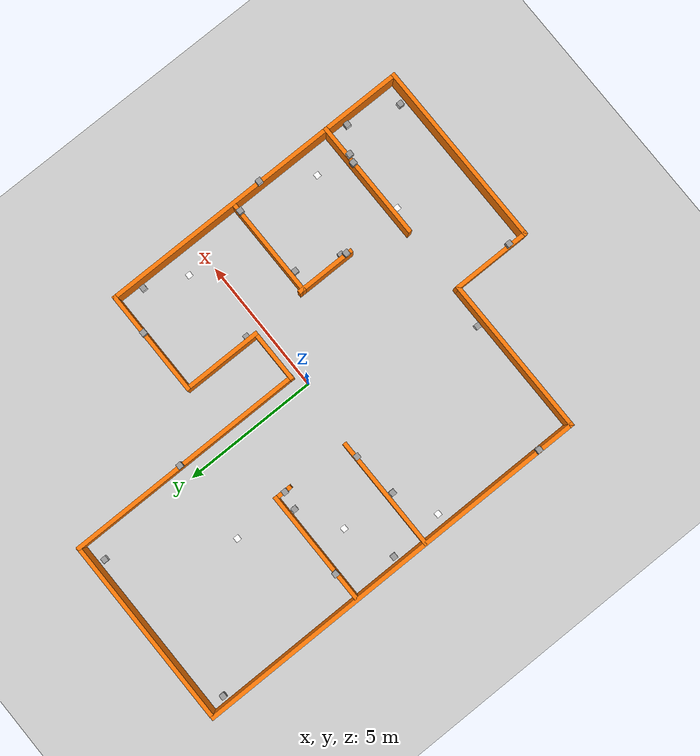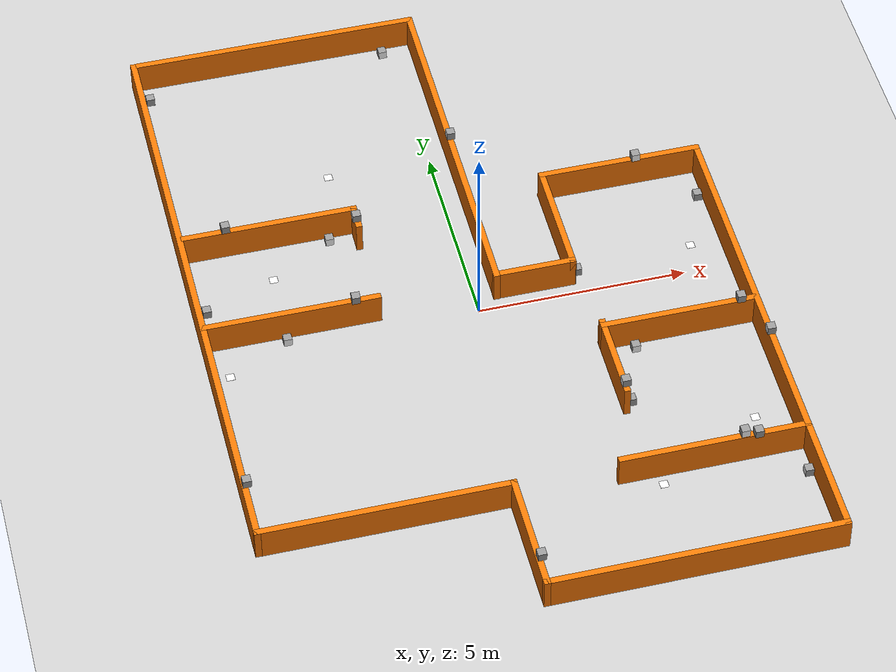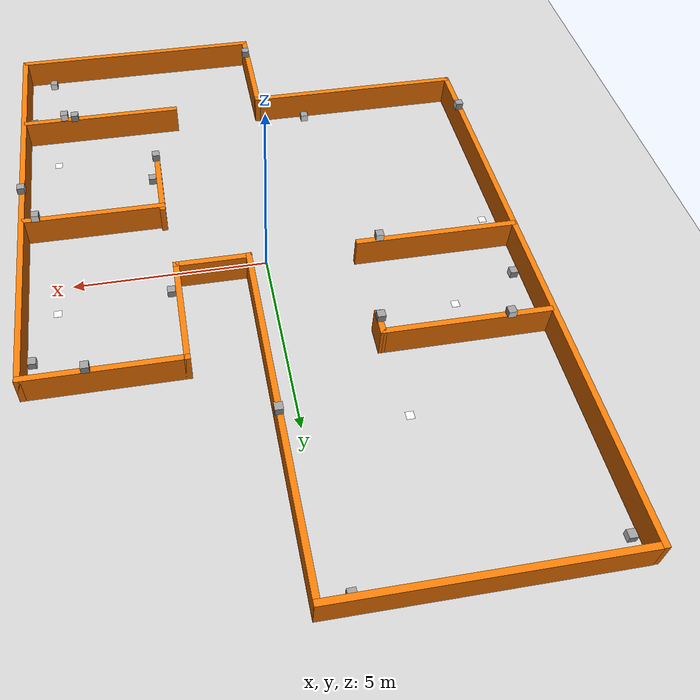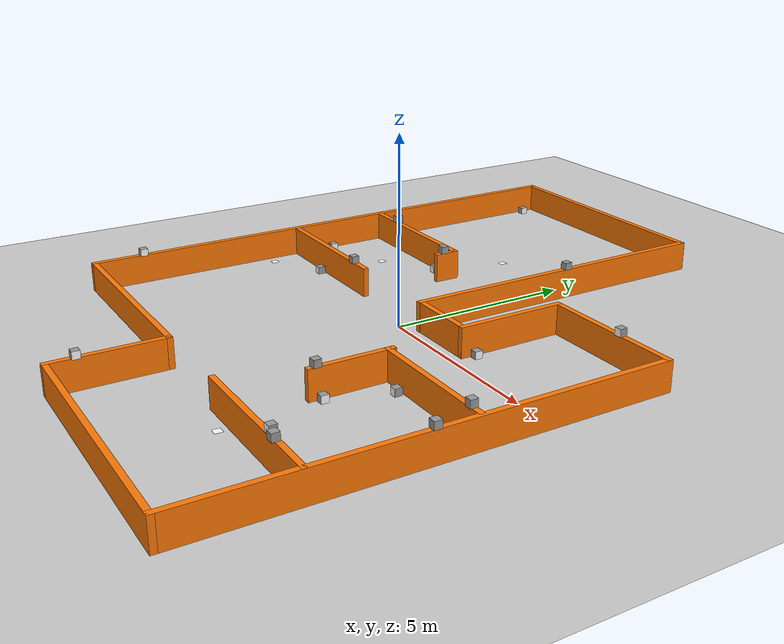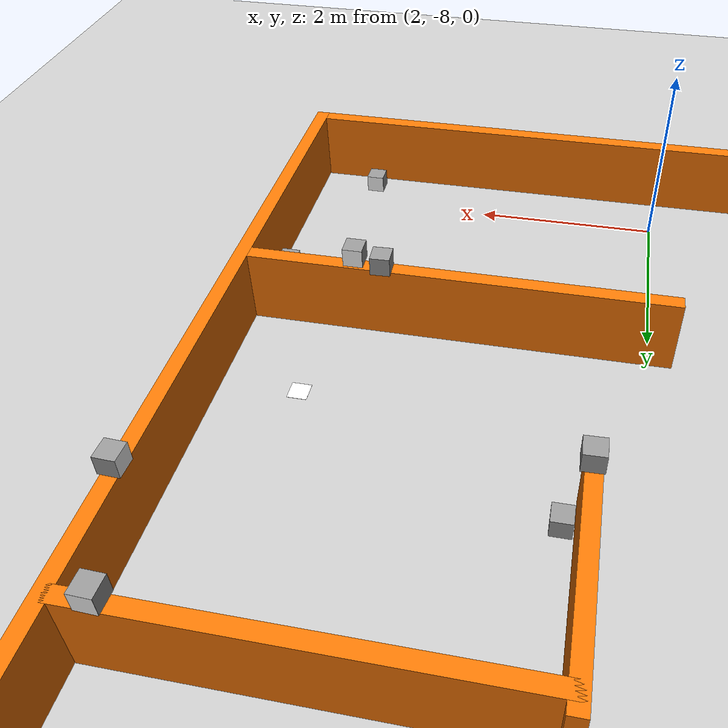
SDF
<sdf version="1.7">
 <world name="default">
  <light name="sun" type="directional">
   <pose>0 0 10 0 -0 0</pose>
   <diffuse>0.8 0.8 0.8 1</diffuse>
   <specular>0.2 0.2 0.2 1</specular>
   <attenuation>
    <range>1000</range>
    <constant>0.9</constant>
    <linear>0.01</linear>
    <quadratic>0.001</quadratic>
   </attenuation>
   <direction>-0.5 0.1 -0.9</direction>
   <spot><inner_angle>0</inner_angle><outer_angle>0</outer_angle><falloff>0</falloff></spot>
  </light>
  <model name="ground_plane">
   <static>1</static>
   <link name="link">
    <collision name="collision">
     <geometry><plane><normal>0 0 1</normal><size>100 100</size></plane></geometry>
     <surface>
      <contact><collide_bitmask>65535</collide_bitmask></contact>
      <friction><ode><mu>100</mu><mu2>50</mu2></ode></friction>
     </surface>
    </collision>
    <visual name="visual">
     <cast_shadows>0</cast_shadows>
     <geometry><plane><normal>0 0 1</normal><size>100 100</size></plane></geometry>
     <material>
      <script><uri>file://media/materials/scripts/gazebo.material</uri><name>Gazebo/Grey</name></script>
     </material>
    </visual>
   </link>
  </model>
  <gravity>0 0 -9.8</gravity>
  <magnetic_field>6e-06 2.3e-05 -4.2e-05</magnetic_field>
  <atmosphere type="adiabatic"/>
  <physics name="default_physics" default="0" type="ode">
   <max_step_size>0.001</max_step_size>
   <real_time_factor>1</real_time_factor>
   <real_time_update_rate>1000</real_time_update_rate>
  </physics>
  <scene><ambient>0.4 0.4 0.4 1</ambient><background>0.7 0.7 0.7 1</background><shadows>0</shadows></scene>
  <spherical_coordinates>
   <surface_model>EARTH_WGS84</surface_model>
   <latitude_deg>0</latitude_deg>
   <longitude_deg>0</longitude_deg>
   <elevation>0</elevation>
   <heading_deg>0</heading_deg>
  </spherical_coordinates>
  <model name="house_1">
   <link name="Wall_43">
    <pose>-2.787 8.425 0 0 -0 0</pose>
    <inertial>
     <mass>1</mass>
     <inertia><ixx>1</ixx><ixy>0</ixy><ixz>0</ixz><iyy>1</iyy><iyz>0</iyz><izz>1</izz></inertia>
    </inertial>
    <visual name="Wall_43_Visual">
     <pose>0 0 0.4 0 -0 0</pose>
     <geometry><box><size>7 0.15 0.8</size></box></geometry>
     <material>
      <script><uri>file://media/materials/scripts/gazebo.material</uri><name>Gazebo/Grey</name></script>
      <ambient>0.996 0.475 0.02 1</ambient>
      <shader type="pixel"><normal_map>__default__</normal_map></shader>
      <diffuse>0.7 0.7 0.7 1</diffuse>
      <specular>0.01 0.01 0.01 1</specular>
      <emissive>0 0 0 1</emissive>
     </material>
     <meta><layer>0</layer></meta>
    </visual>
    <collision name="Wall_43_Collision">
     <pose>0 0 0.4 0 -0 0</pose>
     <geometry><box><size>7 0.15 0.8</size></box></geometry>
     <surface>
      <friction>
       <ode><mu>1</mu><mu2>1</mu2><fdir1>0 0 0</fdir1><slip1>0</slip1><slip2>0</slip2></ode>
       <torsional>
        <coefficient>1</coefficient>
        <patch_radius>0</patch_radius>
        <surface_radius>0</surface_radius>
        <use_patch_radius>1</use_patch_radius>
        <ode><slip>0</slip></ode>
       </torsional>
      </friction>
      <bounce><restitution_coefficient>0</restitution_coefficient><threshold>1e+06</threshold></bounce>
      <contact>
       <collide_without_contact>0</collide_without_contact>
       <collide_without_contact_bitmask>1</collide_without_contact_bitmask>
       <collide_bitmask>1</collide_bitmask>
       <ode>
        <soft_cfm>0</soft_cfm>
        <soft_erp>0.2</soft_erp>
        <kp>1e+13</kp>
        <kd>1</kd>
        <max_vel>0.01</max_vel>
        <min_depth>0</min_depth>
       </ode>
       <bullet>
        <split_impulse>1</split_impulse>
        <split_impulse_penetration_threshold>-0.01</split_impulse_penetration_threshold>
        <soft_cfm>0</soft_cfm>
        <soft_erp>0.2</soft_erp>
        <kp>1e+13</kp>
        <kd>1</kd>
       </bullet>
      </contact>
     </surface>
    </collision>
   </link>
   <link name="Wall_44">
    <pose>0.642 3.99 0 0 0 -1.5708</pose>
    <inertial>
     <mass>1</mass>
     <inertia><ixx>1</ixx><ixy>0</ixy><ixz>0</ixz><iyy>1</iyy><iyz>0</iyz><izz>1</izz></inertia>
    </inertial>
    <visual name="Wall_44_Visual">
     <pose>0 0 0.4 0 -0 0</pose>
     <geometry><box><size>9 0.15 0.8</size></box></geometry>
     <material>
      <script><uri>file://media/materials/scripts/gazebo.material</uri><name>Gazebo/Grey</name></script>
      <ambient>0.996 0.475 0.02 1</ambient>
      <shader type="pixel"><normal_map>__default__</normal_map></shader>
      <diffuse>0.7 0.7 0.7 1</diffuse>
      <specular>0.01 0.01 0.01 1</specular>
      <emissive>0 0 0 1</emissive>
     </material>
     <meta><layer>0</layer></meta>
    </visual>
    <collision name="Wall_44_Collision">
     <pose>0 0 0.4 0 -0 0</pose>
     <geometry><box><size>9 0.15 0.8</size></box></geometry>
     <surface>
      <friction>
       <ode><mu>1</mu><mu2>1</mu2><fdir1>0 0 0</fdir1><slip1>0</slip1><slip2>0</slip2></ode>
       <torsional>
        <coefficient>1</coefficient>
        <patch_radius>0</patch_radius>
        <surface_radius>0</surface_radius>
        <use_patch_radius>1</use_patch_radius>
        <ode><slip>0</slip></ode>
       </torsional>
      </friction>
      <bounce><restitution_coefficient>0</restitution_coefficient><threshold>1e+06</threshold></bounce>
      <contact>
       <collide_without_contact>0</collide_without_contact>
       <collide_without_contact_bitmask>1</collide_without_contact_bitmask>
       <collide_bitmask>1</collide_bitmask>
       <ode>
        <soft_cfm>0</soft_cfm>
        <soft_erp>0.2</soft_erp>
        <kp>1e+13</kp>
        <kd>1</kd>
        <max_vel>0.01</max_vel>
        <min_depth>0</min_depth>
       </ode>
       <bullet>
        <split_impulse>1</split_impulse>
        <split_impulse_penetration_threshold>-0.01</split_impulse_penetration_threshold>
        <soft_cfm>0</soft_cfm>
        <soft_erp>0.2</soft_erp>
        <kp>1e+13</kp>
        <kd>1</kd>
       </bullet>
      </contact>
     </surface>
    </collision>
   </link>
   <link name="Wall_45">
    <pose>1.563 -0.425 0 0 -0 0</pose>
    <inertial>
     <mass>1</mass>
     <inertia><ixx>1</ixx><ixy>0</ixy><ixz>0</ixz><iyy>1</iyy><iyz>0</iyz><izz>1</izz></inertia>
    </inertial>
    <visual name="Wall_45_Visual">
     <pose>0 0 0.4 0 -0 0</pose>
     <geometry><box><size>2 0.15 0.8</size></box></geometry>
     <material>
      <script><uri>file://media/materials/scripts/gazebo.material</uri><name>Gazebo/Grey</name></script>
      <ambient>0.996 0.475 0.02 1</ambient>
      <shader type="pixel"><normal_map>__default__</normal_map></shader>
      <diffuse>0.7 0.7 0.7 1</diffuse>
      <specular>0.01 0.01 0.01 1</specular>
      <emissive>0 0 0 1</emissive>
     </material>
     <meta><layer>0</layer></meta>
    </visual>
    <collision name="Wall_45_Collision">
     <pose>0 0 0.4 0 -0 0</pose>
     <geometry><box><size>2 0.15 0.8</size></box></geometry>
     <surface>
      <friction>
       <ode><mu>1</mu><mu2>1</mu2><fdir1>0 0 0</fdir1><slip1>0</slip1><slip2>0</slip2></ode>
       <torsional>
        <coefficient>1</coefficient>
        <patch_radius>0</patch_radius>
        <surface_radius>0</surface_radius>
        <use_patch_radius>1</use_patch_radius>
        <ode><slip>0</slip></ode>
       </torsional>
      </friction>
      <bounce><restitution_coefficient>0</restitution_coefficient><threshold>1e+06</threshold></bounce>
      <contact>
       <collide_without_contact>0</collide_without_contact>
       <collide_without_contact_bitmask>1</collide_without_contact_bitmask>
       <collide_bitmask>1</collide_bitmask>
       <ode>
        <soft_cfm>0</soft_cfm>
        <soft_erp>0.2</soft_erp>
        <kp>1e+13</kp>
        <kd>1</kd>
        <max_vel>0.01</max_vel>
        <min_depth>0</min_depth>
       </ode>
       <bullet>
        <split_impulse>1</split_impulse>
        <split_impulse_penetration_threshold>-0.01</split_impulse_penetration_threshold>
        <soft_cfm>0</soft_cfm>
        <soft_erp>0.2</soft_erp>
        <kp>1e+13</kp>
        <kd>1</kd>
       </bullet>
      </contact>
     </surface>
    </collision>
   </link>
   <link name="Wall_46">
    <pose>2.488 1 0 0 -0 1.5708</pose>
    <inertial>
     <mass>1</mass>
     <inertia><ixx>1</ixx><ixy>0</ixy><ixz>0</ixz><iyy>1</iyy><iyz>0</iyz><izz>1</izz></inertia>
    </inertial>
    <visual name="Wall_46_Visual">
     <pose>0 0 0.4 0 -0 0</pose>
     <geometry><box><size>3 0.15 0.8</size></box></geometry>
     <material>
      <script><uri>file://media/materials/scripts/gazebo.material</uri><name>Gazebo/Grey</name></script>
      <ambient>0.996 0.475 0.02 1</ambient>
      <shader type="pixel"><normal_map>__default__</normal_map></shader>
      <diffuse>0.7 0.7 0.7 1</diffuse>
      <specular>0.01 0.01 0.01 1</specular>
      <emissive>0 0 0 1</emissive>
     </material>
     <meta><layer>0</layer></meta>
    </visual>
    <collision name="Wall_46_Collision">
     <pose>0 0 0.4 0 -0 0</pose>
     <geometry><box><size>3 0.15 0.8</size></box></geometry>
     <surface>
      <friction>
       <ode><mu>1</mu><mu2>1</mu2><fdir1>0 0 0</fdir1><slip1>0</slip1><slip2>0</slip2></ode>
       <torsional>
        <coefficient>1</coefficient>
        <patch_radius>0</patch_radius>
        <surface_radius>0</surface_radius>
        <use_patch_radius>1</use_patch_radius>
        <ode><slip>0</slip></ode>
       </torsional>
      </friction>
      <bounce><restitution_coefficient>0</restitution_coefficient><threshold>1e+06</threshold></bounce>
      <contact>
       <collide_without_contact>0</collide_without_contact>
       <collide_without_contact_bitmask>1</collide_without_contact_bitmask>
       <collide_bitmask>1</collide_bitmask>
       <ode>
        <soft_cfm>0</soft_cfm>
        <soft_erp>0.2</soft_erp>
        <kp>1e+13</kp>
        <kd>1</kd>
        <max_vel>0.01</max_vel>
        <min_depth>0</min_depth>
       </ode>
       <bullet>
        <split_impulse>1</split_impulse>
        <split_impulse_penetration_threshold>-0.01</split_impulse_penetration_threshold>
        <soft_cfm>0</soft_cfm>
        <soft_erp>0.2</soft_erp>
        <kp>1e+13</kp>
        <kd>1</kd>
       </bullet>
      </contact>
     </surface>
    </collision>
   </link>
   <link name="Wall_47">
    <pose>4.413 2.425 0 0 -0 0</pose>
    <visual name="Wall_47_Visual">
     <pose>0 0 0.4 0 -0 0</pose>
     <geometry><box><size>4 0.15 0.8</size></box></geometry>
     <material>
      <script><uri>file://media/materials/scripts/gazebo.material</uri><name>Gazebo/Grey</name></script>
      <ambient>0.996078 0.47451 0.0196078 1</ambient>
      <shader type="pixel"/>
      <diffuse>0.7 0.7 0.7 1</diffuse>
      <specular>0.01 0.01 0.01 1</specular>
      <emissive>0 0 0 1</emissive>
     </material>
     <meta><layer>0</layer></meta>
    </visual>
    <collision name="Wall_47_Collision">
     <pose>0 0 0.4 0 -0 0</pose>
     <geometry><box><size>4 0.15 0.8</size></box></geometry>
     <surface>
      <friction>
       <ode><mu>1</mu><mu2>1</mu2><fdir1>0 0 0</fdir1><slip1>0</slip1><slip2>0</slip2></ode>
       <torsional>
        <coefficient>1</coefficient>
        <patch_radius>0</patch_radius>
        <surface_radius>0</surface_radius>
        <use_patch_radius>1</use_patch_radius>
        <ode><slip>0</slip></ode>
       </torsional>
      </friction>
      <bounce><restitution_coefficient>0</restitution_coefficient><threshold>1e+06</threshold></bounce>
      <contact>
       <collide_without_contact>0</collide_without_contact>
       <collide_without_contact_bitmask>1</collide_without_contact_bitmask>
       <collide_bitmask>1</collide_bitmask>
       <ode>
        <soft_cfm>0</soft_cfm>
        <soft_erp>0.2</soft_erp>
        <kp>1e+13</kp>
        <kd>1</kd>
        <max_vel>0.01</max_vel>
        <min_depth>0</min_depth>
       </ode>
       <bullet>
        <split_impulse>1</split_impulse>
        <split_impulse_penetration_threshold>-0.01</split_impulse_penetration_threshold>
        <soft_cfm>0</soft_cfm>
        <soft_erp>0.2</soft_erp>
        <kp>1e+13</kp>
        <kd>1</kd>
       </bullet>
      </contact>
     </surface>
    </collision>
   </link>
   <link name="Wall_48">
    <pose>6.338 -3.5 0 0 0 -1.5708</pose>
    <inertial>
     <mass>1</mass>
     <inertia><ixx>1</ixx><ixy>0</ixy><ixz>0</ixz><iyy>1</iyy><iyz>0</iyz><izz>1</izz></inertia>
    </inertial>
    <visual name="Wall_48_Visual">
     <pose>0 0 0.4 0 -0 0</pose>
     <geometry><box><size>12 0.15 0.8</size></box></geometry>
     <material>
      <script><uri>file://media/materials/scripts/gazebo.material</uri><name>Gazebo/Grey</name></script>
      <ambient>0.996 0.475 0.02 1</ambient>
      <shader type="pixel"><normal_map>__default__</normal_map></shader>
      <diffuse>0.7 0.7 0.7 1</diffuse>
      <specular>0.01 0.01 0.01 1</specular>
      <emissive>0 0 0 1</emissive>
     </material>
     <meta><layer>0</layer></meta>
    </visual>
    <collision name="Wall_48_Collision">
     <pose>0 0 0.4 0 -0 0</pose>
     <geometry><box><size>12 0.15 0.8</size></box></geometry>
     <surface>
      <friction>
       <ode><mu>1</mu><mu2>1</mu2><fdir1>0 0 0</fdir1><slip1>0</slip1><slip2>0</slip2></ode>
       <torsional>
        <coefficient>1</coefficient>
        <patch_radius>0</patch_radius>
        <surface_radius>0</surface_radius>
        <use_patch_radius>1</use_patch_radius>
        <ode><slip>0</slip></ode>
       </torsional>
      </friction>
      <bounce><restitution_coefficient>0</restitution_coefficient><threshold>1e+06</threshold></bounce>
      <contact>
       <collide_without_contact>0</collide_without_contact>
       <collide_without_contact_bitmask>1</collide_without_contact_bitmask>
       <collide_bitmask>1</collide_bitmask>
       <ode>
        <soft_cfm>0</soft_cfm>
        <soft_erp>0.2</soft_erp>
        <kp>1e+13</kp>
        <kd>1</kd>
        <max_vel>0.01</max_vel>
        <min_depth>0</min_depth>
       </ode>
       <bullet>
        <split_impulse>1</split_impulse>
        <split_impulse_penetration_threshold>-0.01</split_impulse_penetration_threshold>
        <soft_cfm>0</soft_cfm>
        <soft_erp>0.2</soft_erp>
        <kp>1e+13</kp>
        <kd>1</kd>
       </bullet>
      </contact>
     </surface>
    </collision>
   </link>
   <link name="Wall_49">
    <pose>2.913 -9.425 0 0 -0 3.14159</pose>
    <inertial>
     <mass>1</mass>
     <inertia><ixx>1</ixx><ixy>0</ixy><ixz>0</ixz><iyy>1</iyy><iyz>0</iyz><izz>1</izz></inertia>
    </inertial>
    <visual name="Wall_49_Visual">
     <pose>0 0 0.4 0 -0 0</pose>
     <geometry><box><size>7 0.15 0.8</size></box></geometry>
     <material>
      <script><uri>file://media/materials/scripts/gazebo.material</uri><name>Gazebo/Grey</name></script>
      <ambient>0.996 0.475 0.02 1</ambient>
      <shader type="pixel"><normal_map>__default__</normal_map></shader>
      <diffuse>0.7 0.7 0.7 1</diffuse>
      <specular>0.01 0.01 0.01 1</specular>
      <emissive>0 0 0 1</emissive>
     </material>
     <meta><layer>0</layer></meta>
    </visual>
    <collision name="Wall_49_Collision">
     <pose>0 0 0.4 0 -0 0</pose>
     <geometry><box><size>7 0.15 0.8</size></box></geometry>
     <surface>
      <friction>
       <ode><mu>1</mu><mu2>1</mu2><fdir1>0 0 0</fdir1><slip1>0</slip1><slip2>0</slip2></ode>
       <torsional>
        <coefficient>1</coefficient>
        <patch_radius>0</patch_radius>
        <surface_radius>0</surface_radius>
        <use_patch_radius>1</use_patch_radius>
        <ode><slip>0</slip></ode>
       </torsional>
      </friction>
      <bounce><restitution_coefficient>0</restitution_coefficient><threshold>1e+06</threshold></bounce>
      <contact>
       <collide_without_contact>0</collide_without_contact>
       <collide_without_contact_bitmask>1</collide_without_contact_bitmask>
       <collide_bitmask>1</collide_bitmask>
       <ode>
        <soft_cfm>0</soft_cfm>
        <soft_erp>0.2</soft_erp>
        <kp>1e+13</kp>
        <kd>1</kd>
        <max_vel>0.01</max_vel>
        <min_depth>0</min_depth>
       </ode>
       <bullet>
        <split_impulse>1</split_impulse>
        <split_impulse_penetration_threshold>-0.01</split_impulse_penetration_threshold>
        <soft_cfm>0</soft_cfm>
        <soft_erp>0.2</soft_erp>
        <kp>1e+13</kp>
        <kd>1</kd>
       </bullet>
      </contact>
     </surface>
    </collision>
   </link>
   <link name="Wall_50">
    <pose>-0.512 -8 0 0 -0 1.5708</pose>
    <inertial>
     <mass>1</mass>
     <inertia><ixx>1</ixx><ixy>0</ixy><ixz>0</ixz><iyy>1</iyy><iyz>0</iyz><izz>1</izz></inertia>
    </inertial>
    <visual name="Wall_50_Visual">
     <pose>0 0 0.4 0 -0 0</pose>
     <geometry><box><size>3 0.15 0.8</size></box></geometry>
     <material>
      <script><uri>file://media/materials/scripts/gazebo.material</uri><name>Gazebo/Grey</name></script>
      <ambient>0.996 0.475 0.02 1</ambient>
      <shader type="pixel"><normal_map>__default__</normal_map></shader>
      <diffuse>0.7 0.7 0.7 1</diffuse>
      <specular>0.01 0.01 0.01 1</specular>
      <emissive>0 0 0 1</emissive>
     </material>
     <meta><layer>0</layer></meta>
    </visual>
    <collision name="Wall_50_Collision">
     <pose>0 0 0.4 0 -0 0</pose>
     <geometry><box><size>3 0.15 0.8</size></box></geometry>
     <surface>
      <friction>
       <ode><mu>1</mu><mu2>1</mu2><fdir1>0 0 0</fdir1><slip1>0</slip1><slip2>0</slip2></ode>
       <torsional>
        <coefficient>1</coefficient>
        <patch_radius>0</patch_radius>
        <surface_radius>0</surface_radius>
        <use_patch_radius>1</use_patch_radius>
        <ode><slip>0</slip></ode>
       </torsional>
      </friction>
      <bounce><restitution_coefficient>0</restitution_coefficient><threshold>1e+06</threshold></bounce>
      <contact>
       <collide_without_contact>0</collide_without_contact>
       <collide_without_contact_bitmask>1</collide_without_contact_bitmask>
       <collide_bitmask>1</collide_bitmask>
       <ode>
        <soft_cfm>0</soft_cfm>
        <soft_erp>0.2</soft_erp>
        <kp>1e+13</kp>
        <kd>1</kd>
        <max_vel>0.01</max_vel>
        <min_depth>0</min_depth>
       </ode>
       <bullet>
        <split_impulse>1</split_impulse>
        <split_impulse_penetration_threshold>-0.01</split_impulse_penetration_threshold>
        <soft_cfm>0</soft_cfm>
        <soft_erp>0.2</soft_erp>
        <kp>1e+13</kp>
        <kd>1</kd>
       </bullet>
      </contact>
     </surface>
    </collision>
   </link>
   <link name="Wall_51">
    <pose>-3.425 -6.575 0 0 -0 3.14159</pose>
    <visual name="Wall_51_Visual">
     <pose>0 0 0.4 0 -0 0</pose>
     <geometry><box><size>5.976 0.15 0.8</size></box></geometry>
     <material>
      <script><uri>file://media/materials/scripts/gazebo.material</uri><name>Gazebo/Grey</name></script>
      <ambient>0.996078 0.47451 0.0196078 1</ambient>
      <shader type="pixel"/>
      <diffuse>0.7 0.7 0.7 1</diffuse>
      <specular>0.01 0.01 0.01 1</specular>
      <emissive>0 0 0 1</emissive>
     </material>
     <meta><layer>0</layer></meta>
    </visual>
    <collision name="Wall_51_Collision">
     <pose>0 0 0.4 0 -0 0</pose>
     <geometry><box><size>5.976 0.15 0.8</size></box></geometry>
     <surface>
      <friction>
       <ode><mu>1</mu><mu2>1</mu2><fdir1>0 0 0</fdir1><slip1>0</slip1><slip2>0</slip2></ode>
       <torsional>
        <coefficient>1</coefficient>
        <patch_radius>0</patch_radius>
        <surface_radius>0</surface_radius>
        <use_patch_radius>1</use_patch_radius>
        <ode><slip>0</slip></ode>
       </torsional>
      </friction>
      <bounce><restitution_coefficient>0</restitution_coefficient><threshold>1e+06</threshold></bounce>
      <contact>
       <collide_without_contact>0</collide_without_contact>
       <collide_without_contact_bitmask>1</collide_without_contact_bitmask>
       <collide_bitmask>1</collide_bitmask>
       <ode>
        <soft_cfm>0</soft_cfm>
        <soft_erp>0.2</soft_erp>
        <kp>1e+13</kp>
        <kd>1</kd>
        <max_vel>0.01</max_vel>
        <min_depth>0</min_depth>
       </ode>
       <bullet>
        <split_impulse>1</split_impulse>
        <split_impulse_penetration_threshold>-0.01</split_impulse_penetration_threshold>
        <soft_cfm>0</soft_cfm>
        <soft_erp>0.2</soft_erp>
        <kp>1e+13</kp>
        <kd>1</kd>
       </bullet>
      </contact>
     </surface>
    </collision>
   </link>
   <link name="Wall_52">
    <pose>-6.338 0.9215 0 0 -0 1.5708</pose>
    <visual name="Wall_52_Visual">
     <pose>0 0 0.4 0 -0 0</pose>
     <geometry><box><size>15.1433 0.15 0.8</size></box></geometry>
     <material>
      <script><uri>file://media/materials/scripts/gazebo.material</uri><name>Gazebo/Grey</name></script>
      <ambient>0.996078 0.47451 0.0196078 1</ambient>
      <shader type="pixel"/>
      <diffuse>0.7 0.7 0.7 1</diffuse>
      <specular>0.01 0.01 0.01 1</specular>
      <emissive>0 0 0 1</emissive>
     </material>
     <meta><layer>0</layer></meta>
    </visual>
    <collision name="Wall_52_Collision">
     <pose>0 0 0.4 0 -0 0</pose>
     <geometry><box><size>15.1433 0.15 0.8</size></box></geometry>
     <surface>
      <friction>
       <ode><mu>1</mu><mu2>1</mu2><fdir1>0 0 0</fdir1><slip1>0</slip1><slip2>0</slip2></ode>
       <torsional>
        <coefficient>1</coefficient>
        <patch_radius>0</patch_radius>
        <surface_radius>0</surface_radius>
        <use_patch_radius>1</use_patch_radius>
        <ode><slip>0</slip></ode>
       </torsional>
      </friction>
      <bounce><restitution_coefficient>0</restitution_coefficient><threshold>1e+06</threshold></bounce>
      <contact>
       <collide_without_contact>0</collide_without_contact>
       <collide_without_contact_bitmask>1</collide_without_contact_bitmask>
       <collide_bitmask>1</collide_bitmask>
       <ode>
        <soft_cfm>0</soft_cfm>
        <soft_erp>0.2</soft_erp>
        <kp>1e+13</kp>
        <kd>1</kd>
        <max_vel>0.01</max_vel>
        <min_depth>0</min_depth>
       </ode>
       <bullet>
        <split_impulse>1</split_impulse>
        <split_impulse_penetration_threshold>-0.01</split_impulse_penetration_threshold>
        <soft_cfm>0</soft_cfm>
        <soft_erp>0.2</soft_erp>
        <kp>1e+13</kp>
        <kd>1</kd>
       </bullet>
      </contact>
     </surface>
    </collision>
   </link>
   <link name="Wall_54">
    <pose>-4.182 2.435 0 0 -0 0</pose>
    <visual name="Wall_54_Visual">
     <pose>0 0 0.4 0 -0 0</pose>
     <geometry><box><size>4.25 0.15 0.8</size></box></geometry>
     <material>
      <script><uri>file://media/materials/scripts/gazebo.material</uri><name>Gazebo/Grey</name></script>
      <ambient>0.996078 0.47451 0.0196078 1</ambient>
      <shader type="pixel"/>
      <diffuse>0.7 0.7 0.7 1</diffuse>
      <specular>0.01 0.01 0.01 1</specular>
      <emissive>0 0 0 1</emissive>
     </material>
     <meta><layer>0</layer></meta>
    </visual>
    <collision name="Wall_54_Collision">
     <pose>0 0 0.4 0 -0 0</pose>
     <geometry><box><size>4.25 0.15 0.8</size></box></geometry>
     <surface>
      <friction>
       <ode><mu>1</mu><mu2>1</mu2><fdir1>0 0 0</fdir1><slip1>0</slip1><slip2>0</slip2></ode>
       <torsional>
        <coefficient>1</coefficient>
        <patch_radius>0</patch_radius>
        <surface_radius>0</surface_radius>
        <use_patch_radius>1</use_patch_radius>
        <ode><slip>0</slip></ode>
       </torsional>
      </friction>
      <bounce><restitution_coefficient>0</restitution_coefficient><threshold>1e+06</threshold></bounce>
      <contact>
       <collide_without_contact>0</collide_without_contact>
       <collide_without_contact_bitmask>1</collide_without_contact_bitmask>
       <collide_bitmask>1</collide_bitmask>
       <ode>
        <soft_cfm>0</soft_cfm>
        <soft_erp>0.2</soft_erp>
        <kp>1e+13</kp>
        <kd>1</kd>
        <max_vel>0.01</max_vel>
        <min_depth>0</min_depth>
       </ode>
       <bullet>
        <split_impulse>1</split_impulse>
        <split_impulse_penetration_threshold>-0.01</split_impulse_penetration_threshold>
        <soft_cfm>0</soft_cfm>
        <soft_erp>0.2</soft_erp>
        <kp>1e+13</kp>
        <kd>1</kd>
       </bullet>
      </contact>
     </surface>
    </collision>
   </link>
   <link name="Wall_56">
    <pose>-4.252 -0.433 0 0 -0 0</pose>
    <visual name="Wall_56_Visual">
     <pose>0 0 0.4 0 -0 0</pose>
     <geometry><box><size>4.25 0.15 0.8</size></box></geometry>
     <material>
      <script><uri>file://media/materials/scripts/gazebo.material</uri><name>Gazebo/Grey</name></script>
      <ambient>0.996078 0.47451 0.0196078 1</ambient>
      <shader type="pixel"/>
      <diffuse>0.7 0.7 0.7 1</diffuse>
      <specular>0.01 0.01 0.01 1</specular>
      <emissive>0 0 0 1</emissive>
     </material>
     <meta><layer>0</layer></meta>
    </visual>
    <collision name="Wall_56_Collision">
     <pose>0 0 0.4 0 -0 0</pose>
     <geometry><box><size>4.25 0.15 0.8</size></box></geometry>
     <surface>
      <friction>
       <ode><mu>1</mu><mu2>1</mu2><fdir1>0 0 0</fdir1><slip1>0</slip1><slip2>0</slip2></ode>
       <torsional>
        <coefficient>1</coefficient>
        <patch_radius>0</patch_radius>
        <surface_radius>0</surface_radius>
        <use_patch_radius>1</use_patch_radius>
        <ode><slip>0</slip></ode>
       </torsional>
      </friction>
      <bounce><restitution_coefficient>0</restitution_coefficient><threshold>1e+06</threshold></bounce>
      <contact>
       <collide_without_contact>0</collide_without_contact>
       <collide_without_contact_bitmask>1</collide_without_contact_bitmask>
       <collide_bitmask>1</collide_bitmask>
       <ode>
        <soft_cfm>0</soft_cfm>
        <soft_erp>0.2</soft_erp>
        <kp>1e+13</kp>
        <kd>1</kd>
        <max_vel>0.01</max_vel>
        <min_depth>0</min_depth>
       </ode>
       <bullet>
        <split_impulse>1</split_impulse>
        <split_impulse_penetration_threshold>-0.01</split_impulse_penetration_threshold>
        <soft_cfm>0</soft_cfm>
        <soft_erp>0.2</soft_erp>
        <kp>1e+13</kp>
        <kd>1</kd>
       </bullet>
      </contact>
     </surface>
    </collision>
   </link>
   <link name="Wall_58">
    <pose>-2.132 2.16 0 0 0 -1.5808</pose>
    <inertial>
     <mass>1</mass>
     <inertia><ixx>1</ixx><ixy>0</ixy><ixz>0</ixz><iyy>1</iyy><iyz>0</iyz><izz>1</izz></inertia>
    </inertial>
    <visual name="Wall_58_Visual">
     <pose>0 0 0.4 0 -0 0</pose>
     <geometry><box><size>0.7 0.15 0.8</size></box></geometry>
     <material>
      <script><uri>file://media/materials/scripts/gazebo.material</uri><name>Gazebo/Grey</name></script>
      <ambient>0.996 0.475 0.02 1</ambient>
      <shader type="pixel"><normal_map>__default__</normal_map></shader>
      <diffuse>0.7 0.7 0.7 1</diffuse>
      <specular>0.01 0.01 0.01 1</specular>
      <emissive>0 0 0 1</emissive>
     </material>
     <meta><layer>0</layer></meta>
    </visual>
    <collision name="Wall_58_Collision">
     <pose>0 0 0.4 0 -0 0</pose>
     <geometry><box><size>0.7 0.15 0.8</size></box></geometry>
     <surface>
      <friction>
       <ode><mu>1</mu><mu2>1</mu2><fdir1>0 0 0</fdir1><slip1>0</slip1><slip2>0</slip2></ode>
       <torsional>
        <coefficient>1</coefficient>
        <patch_radius>0</patch_radius>
        <surface_radius>0</surface_radius>
        <use_patch_radius>1</use_patch_radius>
        <ode><slip>0</slip></ode>
       </torsional>
      </friction>
      <bounce><restitution_coefficient>0</restitution_coefficient><threshold>1e+06</threshold></bounce>
      <contact>
       <collide_without_contact>0</collide_without_contact>
       <collide_without_contact_bitmask>1</collide_without_contact_bitmask>
       <collide_bitmask>1</collide_bitmask>
       <ode>
        <soft_cfm>0</soft_cfm>
        <soft_erp>0.2</soft_erp>
        <kp>1e+13</kp>
        <kd>1</kd>
        <max_vel>0.01</max_vel>
        <min_depth>0</min_depth>
       </ode>
       <bullet>
        <split_impulse>1</split_impulse>
        <split_impulse_penetration_threshold>-0.01</split_impulse_penetration_threshold>
        <soft_cfm>0</soft_cfm>
        <soft_erp>0.2</soft_erp>
        <kp>1e+13</kp>
        <kd>1</kd>
       </bullet>
      </contact>
     </surface>
    </collision>
   </link>
   <link name="Wall_60">
    <pose>4.454 -2.562 0 0 -0 3.14159</pose>
    <inertial>
     <mass>1</mass>
     <inertia><ixx>1</ixx><ixy>0</ixy><ixz>0</ixz><iyy>1</iyy><iyz>0</iyz><izz>1</izz></inertia>
    </inertial>
    <visual name="Wall_60_Visual">
     <pose>0 0 0.4 0 -0 0</pose>
     <geometry><box><size>3.75 0.15 0.8</size></box></geometry>
     <material>
      <script><uri>file://media/materials/scripts/gazebo.material</uri><name>Gazebo/Grey</name></script>
      <ambient>0.996 0.475 0.02 1</ambient>
      <shader type="pixel"><normal_map>__default__</normal_map></shader>
      <diffuse>0.7 0.7 0.7 1</diffuse>
      <specular>0.01 0.01 0.01 1</specular>
      <emissive>0 0 0 1</emissive>
     </material>
     <meta><layer>0</layer></meta>
    </visual>
    <collision name="Wall_60_Collision">
     <pose>0 0 0.4 0 -0 0</pose>
     <geometry><box><size>3.75 0.15 0.8</size></box></geometry>
     <surface>
      <friction>
       <ode><mu>1</mu><mu2>1</mu2><fdir1>0 0 0</fdir1><slip1>0</slip1><slip2>0</slip2></ode>
       <torsional>
        <coefficient>1</coefficient>
        <patch_radius>0</patch_radius>
        <surface_radius>0</surface_radius>
        <use_patch_radius>1</use_patch_radius>
        <ode><slip>0</slip></ode>
       </torsional>
      </friction>
      <bounce><restitution_coefficient>0</restitution_coefficient><threshold>1e+06</threshold></bounce>
      <contact>
       <collide_without_contact>0</collide_without_contact>
       <collide_without_contact_bitmask>1</collide_without_contact_bitmask>
       <collide_bitmask>1</collide_bitmask>
       <ode>
        <soft_cfm>0</soft_cfm>
        <soft_erp>0.2</soft_erp>
        <kp>1e+13</kp>
        <kd>1</kd>
        <max_vel>0.01</max_vel>
        <min_depth>0</min_depth>
       </ode>
       <bullet>
        <split_impulse>1</split_impulse>
        <split_impulse_penetration_threshold>-0.01</split_impulse_penetration_threshold>
        <soft_cfm>0</soft_cfm>
        <soft_erp>0.2</soft_erp>
        <kp>1e+13</kp>
        <kd>1</kd>
       </bullet>
      </contact>
     </surface>
    </collision>
   </link>
   <link name="Wall_61">
    <pose>2.654 -3.512 0 0 0 -1.5708</pose>
    <inertial>
     <mass>1</mass>
     <inertia><ixx>1</ixx><ixy>0</ixy><ixz>0</ixz><iyy>1</iyy><iyz>0</iyz><izz>1</izz></inertia>
    </inertial>
    <visual name="Wall_61_Visual">
     <pose>0 0 0.4 0 -0 0</pose>
     <geometry><box><size>2.25 0.15 0.8</size></box></geometry>
     <material>
      <script><uri>file://media/materials/scripts/gazebo.material</uri><name>Gazebo/Grey</name></script>
      <ambient>0.996 0.475 0.02 1</ambient>
      <shader type="pixel"><normal_map>__default__</normal_map></shader>
      <diffuse>0.7 0.7 0.7 1</diffuse>
      <specular>0.01 0.01 0.01 1</specular>
      <emissive>0 0 0 1</emissive>
     </material>
     <meta><layer>0</layer></meta>
    </visual>
    <collision name="Wall_61_Collision">
     <pose>0 0 0.4 0 -0 0</pose>
     <geometry><box><size>2.25 0.15 0.8</size></box></geometry>
     <surface>
      <friction>
       <ode><mu>1</mu><mu2>1</mu2><fdir1>0 0 0</fdir1><slip1>0</slip1><slip2>0</slip2></ode>
       <torsional>
        <coefficient>1</coefficient>
        <patch_radius>0</patch_radius>
        <surface_radius>0</surface_radius>
        <use_patch_radius>1</use_patch_radius>
        <ode><slip>0</slip></ode>
       </torsional>
      </friction>
      <bounce><restitution_coefficient>0</restitution_coefficient><threshold>1e+06</threshold></bounce>
      <contact>
       <collide_without_contact>0</collide_without_contact>
       <collide_without_contact_bitmask>1</collide_without_contact_bitmask>
       <collide_bitmask>1</collide_bitmask>
       <ode>
        <soft_cfm>0</soft_cfm>
        <soft_erp>0.2</soft_erp>
        <kp>1e+13</kp>
        <kd>1</kd>
        <max_vel>0.01</max_vel>
        <min_depth>0</min_depth>
       </ode>
       <bullet>
        <split_impulse>1</split_impulse>
        <split_impulse_penetration_threshold>-0.01</split_impulse_penetration_threshold>
        <soft_cfm>0</soft_cfm>
        <soft_erp>0.2</soft_erp>
        <kp>1e+13</kp>
        <kd>1</kd>
       </bullet>
      </contact>
     </surface>
    </collision>
   </link>
   <link name="Wall_63">
    <pose>4.157 -6.517 0 0 -0 0</pose>
    <inertial>
     <mass>1</mass>
     <inertia><ixx>1</ixx><ixy>0</ixy><ixz>0</ixz><iyy>1</iyy><iyz>0</iyz><izz>1</izz></inertia>
    </inertial>
    <visual name="Wall_63_Visual">
     <pose>0 0 0.4 0 -0 0</pose>
     <geometry><box><size>4.5 0.15 0.8</size></box></geometry>
     <material>
      <script><uri>file://media/materials/scripts/gazebo.material</uri><name>Gazebo/Grey</name></script>
      <ambient>0.996 0.475 0.02 1</ambient>
      <shader type="pixel"><normal_map>__default__</normal_map></shader>
      <diffuse>0.7 0.7 0.7 1</diffuse>
      <specular>0.01 0.01 0.01 1</specular>
      <emissive>0 0 0 1</emissive>
     </material>
     <meta><layer>0</layer></meta>
    </visual>
    <collision name="Wall_63_Collision">
     <pose>0 0 0.4 0 -0 0</pose>
     <geometry><box><size>4.5 0.15 0.8</size></box></geometry>
     <surface>
      <friction>
       <ode><mu>1</mu><mu2>1</mu2><fdir1>0 0 0</fdir1><slip1>0</slip1><slip2>0</slip2></ode>
       <torsional>
        <coefficient>1</coefficient>
        <patch_radius>0</patch_radius>
        <surface_radius>0</surface_radius>
        <use_patch_radius>1</use_patch_radius>
        <ode><slip>0</slip></ode>
       </torsional>
      </friction>
      <bounce><restitution_coefficient>0</restitution_coefficient><threshold>1e+06</threshold></bounce>
      <contact>
       <collide_without_contact>0</collide_without_contact>
       <collide_without_contact_bitmask>1</collide_without_contact_bitmask>
       <collide_bitmask>1</collide_bitmask>
       <ode>
        <soft_cfm>0</soft_cfm>
        <soft_erp>0.2</soft_erp>
        <kp>1e+13</kp>
        <kd>1</kd>
        <max_vel>0.01</max_vel>
        <min_depth>0</min_depth>
       </ode>
       <bullet>
        <split_impulse>1</split_impulse>
        <split_impulse_penetration_threshold>-0.01</split_impulse_penetration_threshold>
        <soft_cfm>0</soft_cfm>
        <soft_erp>0.2</soft_erp>
        <kp>1e+13</kp>
        <kd>1</kd>
       </bullet>
      </contact>
     </surface>
    </collision>
   </link>
   <static>1</static>
   <pose>-0.14491 0.76464 0 0 -0 0</pose>
  </model>
  <model name="marker11_box">
   <link name="marker">
    <inertial>
     <mass>0.1</mass>
     <inertia><ixx>0</ixx><ixy>0</ixy><ixz>0</ixz><iyy>0</iyy><iyz>0</iyz><izz>0</izz></inertia>
    </inertial>
    <self_collide>1</self_collide>
    <pose>-0.76428 -0.101106 0.120004 -0.015494 1.56996 -0.015507</pose>
    <visual name="visual">
     <geometry><box><size>0.2 0.2 0.001</size></box></geometry>
     <material>
      <script>
       <uri>model://marker11/material/scripts</uri>
       <uri>model://marker11/material/textures</uri>
       <name>Aruco/marker11</name>
      </script>
      <shader type="pixel"><normal_map>__default__</normal_map></shader>
      <emissive>0 0 0 1</emissive>
      <ambient>1 1 1 1</ambient>
      <diffuse>1 1 1 1</diffuse>
      <specular>0 0 0 1</specular>
     </material>
    </visual>
    <collision name="collision">
     <geometry><box><size>0.2 0.2 0.02</size></box></geometry>
     <surface>
      <friction>
       <ode><mu>1</mu><mu2>1</mu2><fdir1>0 0 0</fdir1><slip1>0</slip1><slip2>0</slip2></ode>
       <torsional>
        <coefficient>1</coefficient>
        <patch_radius>0</patch_radius>
        <surface_radius>0</surface_radius>
        <use_patch_radius>1</use_patch_radius>
        <ode><slip>0</slip></ode>
       </torsional>
      </friction>
      <bounce><restitution_coefficient>0</restitution_coefficient><threshold>1e+06</threshold></bounce>
      <contact>
       <collide_without_contact>0</collide_without_contact>
       <collide_without_contact_bitmask>1</collide_without_contact_bitmask>
       <collide_bitmask>1</collide_bitmask>
       <ode>
        <soft_cfm>0</soft_cfm>
        <soft_erp>0.2</soft_erp>
        <kp>1e+13</kp>
        <kd>1</kd>
        <max_vel>0.01</max_vel>
        <min_depth>0</min_depth>
       </ode>
       <bullet>
        <split_impulse>1</split_impulse>
        <split_impulse_penetration_threshold>-0.01</split_impulse_penetration_threshold>
        <soft_cfm>0</soft_cfm>
        <soft_erp>0.2</soft_erp>
        <kp>1e+13</kp>
        <kd>1</kd>
       </bullet>
      </contact>
     </surface>
    </collision>
   </link>
   <link name="link_1">
    <inertial>
     <mass>1</mass>
     <inertia>
      <ixx>0.166667</ixx>
      <ixy>0</ixy>
      <ixz>0</ixz>
      <iyy>0.166667</iyy>
      <iyz>0</iyz>
      <izz>0.166667</izz>
     </inertia>
    </inertial>
    <pose>-0.86428 -0.101106 0.12 -1.3e-05 -4.2e-05 0</pose>
    <visual name="visual">
     <geometry><box><size>0.2 0.2 0.2</size></box></geometry>
     <material>
      <lighting>1</lighting>
      <script><uri>file://media/materials/scripts/gazebo.material</uri><name>Gazebo/Grey</name></script>
      <shader type="pixel"><normal_map>__default__</normal_map></shader>
      <emissive>0 0 0 1</emissive>
      <ambient>0.3 0.3 0.3 1</ambient>
      <diffuse>0.7 0.7 0.7 1</diffuse>
      <specular>0.01 0.01 0.01 1</specular>
     </material>
    </visual>
    <collision name="collision">
     <geometry><box><size>0.2 0.2 0.2</size></box></geometry>
     <surface>
      <friction>
       <ode><mu>1</mu><mu2>1</mu2><fdir1>0 0 0</fdir1><slip1>0</slip1><slip2>0</slip2></ode>
       <torsional>
        <coefficient>1</coefficient>
        <patch_radius>0</patch_radius>
        <surface_radius>0</surface_radius>
        <use_patch_radius>1</use_patch_radius>
        <ode><slip>0</slip></ode>
       </torsional>
      </friction>
      <bounce><restitution_coefficient>0</restitution_coefficient><threshold>1e+06</threshold></bounce>
      <contact>
       <collide_without_contact>0</collide_without_contact>
       <collide_without_contact_bitmask>1</collide_without_contact_bitmask>
       <collide_bitmask>1</collide_bitmask>
       <ode>
        <soft_cfm>0</soft_cfm>
        <soft_erp>0.2</soft_erp>
        <kp>1e+13</kp>
        <kd>1</kd>
        <max_vel>0.01</max_vel>
        <min_depth>0</min_depth>
       </ode>
       <bullet>
        <split_impulse>1</split_impulse>
        <split_impulse_penetration_threshold>-0.01</split_impulse_penetration_threshold>
        <soft_cfm>0</soft_cfm>
        <soft_erp>0.2</soft_erp>
        <kp>1e+13</kp>
        <kd>1</kd>
       </bullet>
      </contact>
     </surface>
    </collision>
   </link>
   <joint name="link_1_JOINT_3" type="fixed">
    <parent>link_1</parent>
    <child>marker</child>
    <physics>
     <ode><limit><cfm>0</cfm><erp>0.2</erp></limit><suspension><cfm>0</cfm><erp>0.2</erp></suspension></ode>
    </physics>
   </joint>
   <static>0</static>
   <pose>-5.35513 8.733 -0.020009 2e-05 2e-05 0.000591</pose>
  </model>
  <model name="marker12_box">
   <link name="marker">
    <inertial>
     <mass>0.1</mass>
     <inertia><ixx>0</ixx><ixy>0</ixy><ixz>0</ixz><iyy>0</iyy><iyz>0</iyz><izz>0</izz></inertia>
    </inertial>
    <self_collide>1</self_collide>
    <pose>-0.76428 -0.101106 0.120004 -0.015494 1.56996 -0.015507</pose>
    <visual name="visual">
     <geometry><box><size>0.2 0.2 0.001</size></box></geometry>
     <material>
      <script>
       <uri>model://marker12/material/scripts</uri>
       <uri>model://marker12/material/textures</uri>
       <name>Aruco/marker12</name>
      </script>
      <shader type="pixel"><normal_map>__default__</normal_map></shader>
      <emissive>0 0 0 1</emissive>
      <ambient>1 1 1 1</ambient>
      <diffuse>1 1 1 1</diffuse>
      <specular>0 0 0 1</specular>
     </material>
    </visual>
    <collision name="collision">
     <geometry><box><size>0.2 0.2 0.02</size></box></geometry>
     <surface>
      <friction>
       <ode><mu>1</mu><mu2>1</mu2><fdir1>0 0 0</fdir1><slip1>0</slip1><slip2>0</slip2></ode>
       <torsional>
        <coefficient>1</coefficient>
        <patch_radius>0</patch_radius>
        <surface_radius>0</surface_radius>
        <use_patch_radius>1</use_patch_radius>
        <ode><slip>0</slip></ode>
       </torsional>
      </friction>
      <bounce><restitution_coefficient>0</restitution_coefficient><threshold>1e+06</threshold></bounce>
      <contact>
       <collide_without_contact>0</collide_without_contact>
       <collide_without_contact_bitmask>1</collide_without_contact_bitmask>
       <collide_bitmask>1</collide_bitmask>
       <ode>
        <soft_cfm>0</soft_cfm>
        <soft_erp>0.2</soft_erp>
        <kp>1e+13</kp>
        <kd>1</kd>
        <max_vel>0.01</max_vel>
        <min_depth>0</min_depth>
       </ode>
       <bullet>
        <split_impulse>1</split_impulse>
        <split_impulse_penetration_threshold>-0.01</split_impulse_penetration_threshold>
        <soft_cfm>0</soft_cfm>
        <soft_erp>0.2</soft_erp>
        <kp>1e+13</kp>
        <kd>1</kd>
       </bullet>
      </contact>
     </surface>
    </collision>
   </link>
   <link name="link_1">
    <inertial>
     <mass>1</mass>
     <inertia>
      <ixx>0.166667</ixx>
      <ixy>0</ixy>
      <ixz>0</ixz>
      <iyy>0.166667</iyy>
      <iyz>0</iyz>
      <izz>0.166667</izz>
     </inertia>
    </inertial>
    <pose>-0.86428 -0.101106 0.12 -1.3e-05 -4.2e-05 0</pose>
    <visual name="visual">
     <geometry><box><size>0.2 0.2 0.2</size></box></geometry>
     <material>
      <lighting>1</lighting>
      <script><uri>file://media/materials/scripts/gazebo.material</uri><name>Gazebo/Grey</name></script>
      <shader type="pixel"><normal_map>__default__</normal_map></shader>
      <emissive>0 0 0 1</emissive>
      <ambient>0.3 0.3 0.3 1</ambient>
      <diffuse>0.7 0.7 0.7 1</diffuse>
      <specular>0.01 0.01 0.01 1</specular>
     </material>
    </visual>
    <collision name="collision">
     <geometry><box><size>0.2 0.2 0.2</size></box></geometry>
     <surface>
      <friction>
       <ode><mu>1</mu><mu2>1</mu2><fdir1>0 0 0</fdir1><slip1>0</slip1><slip2>0</slip2></ode>
       <torsional>
        <coefficient>1</coefficient>
        <patch_radius>0</patch_radius>
        <surface_radius>0</surface_radius>
        <use_patch_radius>1</use_patch_radius>
        <ode><slip>0</slip></ode>
       </torsional>
      </friction>
      <bounce><restitution_coefficient>0</restitution_coefficient><threshold>1e+06</threshold></bounce>
      <contact>
       <collide_without_contact>0</collide_without_contact>
       <collide_without_contact_bitmask>1</collide_without_contact_bitmask>
       <collide_bitmask>1</collide_bitmask>
       <ode>
        <soft_cfm>0</soft_cfm>
        <soft_erp>0.2</soft_erp>
        <kp>1e+13</kp>
        <kd>1</kd>
        <max_vel>0.01</max_vel>
        <min_depth>0</min_depth>
       </ode>
       <bullet>
        <split_impulse>1</split_impulse>
        <split_impulse_penetration_threshold>-0.01</split_impulse_penetration_threshold>
        <soft_cfm>0</soft_cfm>
        <soft_erp>0.2</soft_erp>
        <kp>1e+13</kp>
        <kd>1</kd>
       </bullet>
      </contact>
     </surface>
    </collision>
   </link>
   <joint name="link_1_JOINT_3" type="fixed">
    <parent>link_1</parent>
    <child>marker</child>
    <physics>
     <ode><limit><cfm>0</cfm><erp>0.2</erp></limit><suspension><cfm>0</cfm><erp>0.2</erp></suspension></ode>
    </physics>
   </joint>
   <static>0</static>
   <pose>-2.96258 1.16251 0.780005 1.3e-05 0 1.5506</pose>
  </model>
  <model name="marker13_box">
   <link name="marker">
    <inertial>
     <mass>0.1</mass>
     <inertia><ixx>0</ixx><ixy>0</ixy><ixz>0</ixz><iyy>0</iyy><iyz>0</iyz><izz>0</izz></inertia>
    </inertial>
    <self_collide>1</self_collide>
    <pose>-0.76428 -0.101106 0.120004 -0.015494 1.56996 -0.015507</pose>
    <visual name="visual">
     <geometry><box><size>0.2 0.2 0.001</size></box></geometry>
     <material>
      <script>
       <uri>model://marker13/material/scripts</uri>
       <uri>model://marker13/material/textures</uri>
       <name>Aruco/marker13</name>
      </script>
      <shader type="pixel"><normal_map>__default__</normal_map></shader>
      <emissive>0 0 0 1</emissive>
      <ambient>1 1 1 1</ambient>
      <diffuse>1 1 1 1</diffuse>
      <specular>0 0 0 1</specular>
     </material>
    </visual>
    <collision name="collision">
     <geometry><box><size>0.2 0.2 0.02</size></box></geometry>
     <surface>
      <friction>
       <ode><mu>1</mu><mu2>1</mu2><fdir1>0 0 0</fdir1><slip1>0</slip1><slip2>0</slip2></ode>
       <torsional>
        <coefficient>1</coefficient>
        <patch_radius>0</patch_radius>
        <surface_radius>0</surface_radius>
        <use_patch_radius>1</use_patch_radius>
        <ode><slip>0</slip></ode>
       </torsional>
      </friction>
      <bounce><restitution_coefficient>0</restitution_coefficient><threshold>1e+06</threshold></bounce>
      <contact>
       <collide_without_contact>0</collide_without_contact>
       <collide_without_contact_bitmask>1</collide_without_contact_bitmask>
       <collide_bitmask>1</collide_bitmask>
       <ode>
        <soft_cfm>0</soft_cfm>
        <soft_erp>0.2</soft_erp>
        <kp>1e+13</kp>
        <kd>1</kd>
        <max_vel>0.01</max_vel>
        <min_depth>0</min_depth>
       </ode>
       <bullet>
        <split_impulse>1</split_impulse>
        <split_impulse_penetration_threshold>-0.01</split_impulse_penetration_threshold>
        <soft_cfm>0</soft_cfm>
        <soft_erp>0.2</soft_erp>
        <kp>1e+13</kp>
        <kd>1</kd>
       </bullet>
      </contact>
     </surface>
    </collision>
   </link>
   <link name="link_1">
    <inertial>
     <mass>1</mass>
     <inertia>
      <ixx>0.166667</ixx>
      <ixy>0</ixy>
      <ixz>0</ixz>
      <iyy>0.166667</iyy>
      <iyz>0</iyz>
      <izz>0.166667</izz>
     </inertia>
    </inertial>
    <pose>-0.86428 -0.101106 0.12 -1.3e-05 -4.2e-05 0</pose>
    <visual name="visual">
     <geometry><box><size>0.2 0.2 0.2</size></box></geometry>
     <material>
      <lighting>1</lighting>
      <script><uri>file://media/materials/scripts/gazebo.material</uri><name>Gazebo/Grey</name></script>
      <shader type="pixel"><normal_map>__default__</normal_map></shader>
      <emissive>0 0 0 1</emissive>
      <ambient>0.3 0.3 0.3 1</ambient>
      <diffuse>0.7 0.7 0.7 1</diffuse>
      <specular>0.01 0.01 0.01 1</specular>
     </material>
    </visual>
    <collision name="collision">
     <geometry><box><size>0.2 0.2 0.2</size></box></geometry>
     <surface>
      <friction>
       <ode><mu>1</mu><mu2>1</mu2><fdir1>0 0 0</fdir1><slip1>0</slip1><slip2>0</slip2></ode>
       <torsional>
        <coefficient>1</coefficient>
        <patch_radius>0</patch_radius>
        <surface_radius>0</surface_radius>
        <use_patch_radius>1</use_patch_radius>
        <ode><slip>0</slip></ode>
       </torsional>
      </friction>
      <bounce><restitution_coefficient>0</restitution_coefficient><threshold>1e+06</threshold></bounce>
      <contact>
       <collide_without_contact>0</collide_without_contact>
       <collide_without_contact_bitmask>1</collide_without_contact_bitmask>
       <collide_bitmask>1</collide_bitmask>
       <ode>
        <soft_cfm>0</soft_cfm>
        <soft_erp>0.2</soft_erp>
        <kp>1e+13</kp>
        <kd>1</kd>
        <max_vel>0.01</max_vel>
        <min_depth>0</min_depth>
       </ode>
       <bullet>
        <split_impulse>1</split_impulse>
        <split_impulse_penetration_threshold>-0.01</split_impulse_penetration_threshold>
        <soft_cfm>0</soft_cfm>
        <soft_erp>0.2</soft_erp>
        <kp>1e+13</kp>
        <kd>1</kd>
       </bullet>
      </contact>
     </surface>
    </collision>
   </link>
   <joint name="link_1_JOINT_3" type="fixed">
    <parent>link_1</parent>
    <child>marker</child>
    <physics>
     <ode><limit><cfm>0</cfm><erp>0.2</erp></limit><suspension><cfm>0</cfm><erp>0.2</erp></suspension></ode>
    </physics>
   </joint>
   <static>0</static>
   <pose>-4.45981 -0.750297 -0.020009 -4e-06 1.8e-05 -1.5676</pose>
  </model>
  <model name="marker14_box">
   <link name="marker">
    <inertial>
     <mass>0.1</mass>
     <inertia><ixx>0</ixx><ixy>0</ixy><ixz>0</ixz><iyy>0</iyy><iyz>0</iyz><izz>0</izz></inertia>
    </inertial>
    <self_collide>1</self_collide>
    <pose>-0.76428 -0.101106 0.120004 -0.015494 1.56996 -0.015507</pose>
    <visual name="visual">
     <geometry><box><size>0.2 0.2 0.001</size></box></geometry>
     <material>
      <script>
       <uri>model://marker14/material/scripts</uri>
       <uri>model://marker14/material/textures</uri>
       <name>Aruco/marker14</name>
      </script>
      <shader type="pixel"><normal_map>__default__</normal_map></shader>
      <emissive>0 0 0 1</emissive>
      <ambient>1 1 1 1</ambient>
      <diffuse>1 1 1 1</diffuse>
      <specular>0 0 0 1</specular>
     </material>
    </visual>
    <collision name="collision">
     <geometry><box><size>0.2 0.2 0.02</size></box></geometry>
     <surface>
      <friction>
       <ode><mu>1</mu><mu2>1</mu2><fdir1>0 0 0</fdir1><slip1>0</slip1><slip2>0</slip2></ode>
       <torsional>
        <coefficient>1</coefficient>
        <patch_radius>0</patch_radius>
        <surface_radius>0</surface_radius>
        <use_patch_radius>1</use_patch_radius>
        <ode><slip>0</slip></ode>
       </torsional>
      </friction>
      <bounce><restitution_coefficient>0</restitution_coefficient><threshold>1e+06</threshold></bounce>
      <contact>
       <collide_without_contact>0</collide_without_contact>
       <collide_without_contact_bitmask>1</collide_without_contact_bitmask>
       <collide_bitmask>1</collide_bitmask>
       <ode>
        <soft_cfm>0</soft_cfm>
        <soft_erp>0.2</soft_erp>
        <kp>1e+13</kp>
        <kd>1</kd>
        <max_vel>0.01</max_vel>
        <min_depth>0</min_depth>
       </ode>
       <bullet>
        <split_impulse>1</split_impulse>
        <split_impulse_penetration_threshold>-0.01</split_impulse_penetration_threshold>
        <soft_cfm>0</soft_cfm>
        <soft_erp>0.2</soft_erp>
        <kp>1e+13</kp>
        <kd>1</kd>
       </bullet>
      </contact>
     </surface>
    </collision>
   </link>
   <link name="link_1">
    <inertial>
     <mass>1</mass>
     <inertia>
      <ixx>0.166667</ixx>
      <ixy>0</ixy>
      <ixz>0</ixz>
      <iyy>0.166667</iyy>
      <iyz>0</iyz>
      <izz>0.166667</izz>
     </inertia>
    </inertial>
    <pose>-0.86428 -0.101106 0.12 -1.3e-05 -4.2e-05 0</pose>
    <visual name="visual">
     <geometry><box><size>0.2 0.2 0.2</size></box></geometry>
     <material>
      <lighting>1</lighting>
      <script><uri>file://media/materials/scripts/gazebo.material</uri><name>Gazebo/Grey</name></script>
      <shader type="pixel"><normal_map>__default__</normal_map></shader>
      <emissive>0 0 0 1</emissive>
      <ambient>0.3 0.3 0.3 1</ambient>
      <diffuse>0.7 0.7 0.7 1</diffuse>
      <specular>0.01 0.01 0.01 1</specular>
     </material>
    </visual>
    <collision name="collision">
     <geometry><box><size>0.2 0.2 0.2</size></box></geometry>
     <surface>
      <friction>
       <ode><mu>1</mu><mu2>1</mu2><fdir1>0 0 0</fdir1><slip1>0</slip1><slip2>0</slip2></ode>
       <torsional>
        <coefficient>1</coefficient>
        <patch_radius>0</patch_radius>
        <surface_radius>0</surface_radius>
        <use_patch_radius>1</use_patch_radius>
        <ode><slip>0</slip></ode>
       </torsional>
      </friction>
      <bounce><restitution_coefficient>0</restitution_coefficient><threshold>1e+06</threshold></bounce>
      <contact>
       <collide_without_contact>0</collide_without_contact>
       <collide_without_contact_bitmask>1</collide_without_contact_bitmask>
       <collide_bitmask>1</collide_bitmask>
       <ode>
        <soft_cfm>0</soft_cfm>
        <soft_erp>0.2</soft_erp>
        <kp>1e+13</kp>
        <kd>1</kd>
        <max_vel>0.01</max_vel>
        <min_depth>0</min_depth>
       </ode>
       <bullet>
        <split_impulse>1</split_impulse>
        <split_impulse_penetration_threshold>-0.01</split_impulse_penetration_threshold>
        <soft_cfm>0</soft_cfm>
        <soft_erp>0.2</soft_erp>
        <kp>1e+13</kp>
        <kd>1</kd>
       </bullet>
      </contact>
     </surface>
    </collision>
   </link>
   <joint name="link_1_JOINT_3" type="fixed">
    <parent>link_1</parent>
    <child>marker</child>
    <physics>
     <ode><limit><cfm>0</cfm><erp>0.2</erp></limit><suspension><cfm>0</cfm><erp>0.2</erp></suspension></ode>
    </physics>
   </joint>
   <static>0</static>
   <pose>4.7652 2.31076 0.779969 1e-05 3.8e-05 -1.55764</pose>
  </model>
  <model name="marker15_box">
   <link name="marker">
    <inertial>
     <mass>0.1</mass>
     <inertia><ixx>0</ixx><ixy>0</ixy><ixz>0</ixz><iyy>0</iyy><iyz>0</iyz><izz>0</izz></inertia>
    </inertial>
    <self_collide>1</self_collide>
    <pose>-0.76428 -0.101106 0.120004 -0.015494 1.56996 -0.015507</pose>
    <visual name="visual">
     <geometry><box><size>0.2 0.2 0.001</size></box></geometry>
     <material>
      <script>
       <uri>model://marker15/material/scripts</uri>
       <uri>model://marker15/material/textures</uri>
       <name>Aruco/marker15</name>
      </script>
      <shader type="pixel"><normal_map>__default__</normal_map></shader>
      <emissive>0 0 0 1</emissive>
      <ambient>1 1 1 1</ambient>
      <diffuse>1 1 1 1</diffuse>
      <specular>0 0 0 1</specular>
     </material>
    </visual>
    <collision name="collision">
     <geometry><box><size>0.2 0.2 0.02</size></box></geometry>
     <surface>
      <friction>
       <ode><mu>1</mu><mu2>1</mu2><fdir1>0 0 0</fdir1><slip1>0</slip1><slip2>0</slip2></ode>
       <torsional>
        <coefficient>1</coefficient>
        <patch_radius>0</patch_radius>
        <surface_radius>0</surface_radius>
        <use_patch_radius>1</use_patch_radius>
        <ode><slip>0</slip></ode>
       </torsional>
      </friction>
      <bounce><restitution_coefficient>0</restitution_coefficient><threshold>1e+06</threshold></bounce>
      <contact>
       <collide_without_contact>0</collide_without_contact>
       <collide_without_contact_bitmask>1</collide_without_contact_bitmask>
       <collide_bitmask>1</collide_bitmask>
       <ode>
        <soft_cfm>0</soft_cfm>
        <soft_erp>0.2</soft_erp>
        <kp>1e+13</kp>
        <kd>1</kd>
        <max_vel>0.01</max_vel>
        <min_depth>0</min_depth>
       </ode>
       <bullet>
        <split_impulse>1</split_impulse>
        <split_impulse_penetration_threshold>-0.01</split_impulse_penetration_threshold>
        <soft_cfm>0</soft_cfm>
        <soft_erp>0.2</soft_erp>
        <kp>1e+13</kp>
        <kd>1</kd>
       </bullet>
      </contact>
     </surface>
    </collision>
   </link>
   <link name="link_1">
    <inertial>
     <mass>1</mass>
     <inertia>
      <ixx>0.166667</ixx>
      <ixy>0</ixy>
      <ixz>0</ixz>
      <iyy>0.166667</iyy>
      <iyz>0</iyz>
      <izz>0.166667</izz>
     </inertia>
    </inertial>
    <pose>-0.86428 -0.101106 0.12 -1.3e-05 -4.2e-05 0</pose>
    <visual name="visual">
     <geometry><box><size>0.2 0.2 0.2</size></box></geometry>
     <material>
      <lighting>1</lighting>
      <script><uri>file://media/materials/scripts/gazebo.material</uri><name>Gazebo/Grey</name></script>
      <shader type="pixel"><normal_map>__default__</normal_map></shader>
      <emissive>0 0 0 1</emissive>
      <ambient>0.3 0.3 0.3 1</ambient>
      <diffuse>0.7 0.7 0.7 1</diffuse>
      <specular>0.01 0.01 0.01 1</specular>
     </material>
    </visual>
    <collision name="collision">
     <geometry><box><size>0.2 0.2 0.2</size></box></geometry>
     <surface>
      <friction>
       <ode><mu>1</mu><mu2>1</mu2><fdir1>0 0 0</fdir1><slip1>0</slip1><slip2>0</slip2></ode>
       <torsional>
        <coefficient>1</coefficient>
        <patch_radius>0</patch_radius>
        <surface_radius>0</surface_radius>
        <use_patch_radius>1</use_patch_radius>
        <ode><slip>0</slip></ode>
       </torsional>
      </friction>
      <bounce><restitution_coefficient>0</restitution_coefficient><threshold>1e+06</threshold></bounce>
      <contact>
       <collide_without_contact>0</collide_without_contact>
       <collide_without_contact_bitmask>1</collide_without_contact_bitmask>
       <collide_bitmask>1</collide_bitmask>
       <ode>
        <soft_cfm>0</soft_cfm>
        <soft_erp>0.2</soft_erp>
        <kp>1e+13</kp>
        <kd>1</kd>
        <max_vel>0.01</max_vel>
        <min_depth>0</min_depth>
       </ode>
       <bullet>
        <split_impulse>1</split_impulse>
        <split_impulse_penetration_threshold>-0.01</split_impulse_penetration_threshold>
        <soft_cfm>0</soft_cfm>
        <soft_erp>0.2</soft_erp>
        <kp>1e+13</kp>
        <kd>1</kd>
       </bullet>
      </contact>
     </surface>
    </collision>
   </link>
   <joint name="link_1_JOINT_3" type="fixed">
    <parent>link_1</parent>
    <child>marker</child>
    <physics>
     <ode><limit><cfm>0</cfm><erp>0.2</erp></limit><suspension><cfm>0</cfm><erp>0.2</erp></suspension></ode>
    </physics>
   </joint>
   <static>0</static>
   <pose>3.33723 -2.88965 -0.020008 1e-05 1.8e-05 -1.56769</pose>
  </model>
  <model name="marker16_box">
   <link name="marker">
    <inertial>
     <mass>0.1</mass>
     <inertia><ixx>0</ixx><ixy>0</ixy><ixz>0</ixz><iyy>0</iyy><iyz>0</iyz><izz>0</izz></inertia>
    </inertial>
    <self_collide>1</self_collide>
    <pose>-0.76428 -0.101106 0.120004 -0.015494 1.56996 -0.015507</pose>
    <visual name="visual">
     <geometry><box><size>0.2 0.2 0.001</size></box></geometry>
     <material>
      <script>
       <uri>model://marker16/material/scripts</uri>
       <uri>model://marker16/material/textures</uri>
       <name>Aruco/marker16</name>
      </script>
      <shader type="pixel"><normal_map>__default__</normal_map></shader>
      <emissive>0 0 0 1</emissive>
      <ambient>1 1 1 1</ambient>
      <diffuse>1 1 1 1</diffuse>
      <specular>0 0 0 1</specular>
     </material>
    </visual>
    <collision name="collision">
     <geometry><box><size>0.2 0.2 0.02</size></box></geometry>
     <surface>
      <friction>
       <ode><mu>1</mu><mu2>1</mu2><fdir1>0 0 0</fdir1><slip1>0</slip1><slip2>0</slip2></ode>
       <torsional>
        <coefficient>1</coefficient>
        <patch_radius>0</patch_radius>
        <surface_radius>0</surface_radius>
        <use_patch_radius>1</use_patch_radius>
        <ode><slip>0</slip></ode>
       </torsional>
      </friction>
      <bounce><restitution_coefficient>0</restitution_coefficient><threshold>1e+06</threshold></bounce>
      <contact>
       <collide_without_contact>0</collide_without_contact>
       <collide_without_contact_bitmask>1</collide_without_contact_bitmask>
       <collide_bitmask>1</collide_bitmask>
       <ode>
        <soft_cfm>0</soft_cfm>
        <soft_erp>0.2</soft_erp>
        <kp>1e+13</kp>
        <kd>1</kd>
        <max_vel>0.01</max_vel>
        <min_depth>0</min_depth>
       </ode>
       <bullet>
        <split_impulse>1</split_impulse>
        <split_impulse_penetration_threshold>-0.01</split_impulse_penetration_threshold>
        <soft_cfm>0</soft_cfm>
        <soft_erp>0.2</soft_erp>
        <kp>1e+13</kp>
        <kd>1</kd>
       </bullet>
      </contact>
     </surface>
    </collision>
   </link>
   <link name="link_1">
    <inertial>
     <mass>1</mass>
     <inertia>
      <ixx>0.166667</ixx>
      <ixy>0</ixy>
      <ixz>0</ixz>
      <iyy>0.166667</iyy>
      <iyz>0</iyz>
      <izz>0.166667</izz>
     </inertia>
    </inertial>
    <pose>-0.86428 -0.101106 0.12 -1.3e-05 -4.2e-05 0</pose>
    <visual name="visual">
     <geometry><box><size>0.2 0.2 0.2</size></box></geometry>
     <material>
      <lighting>1</lighting>
      <script><uri>file://media/materials/scripts/gazebo.material</uri><name>Gazebo/Grey</name></script>
      <shader type="pixel"><normal_map>__default__</normal_map></shader>
      <emissive>0 0 0 1</emissive>
      <ambient>0.3 0.3 0.3 1</ambient>
      <diffuse>0.7 0.7 0.7 1</diffuse>
      <specular>0.01 0.01 0.01 1</specular>
     </material>
    </visual>
    <collision name="collision">
     <geometry><box><size>0.2 0.2 0.2</size></box></geometry>
     <surface>
      <friction>
       <ode><mu>1</mu><mu2>1</mu2><fdir1>0 0 0</fdir1><slip1>0</slip1><slip2>0</slip2></ode>
       <torsional>
        <coefficient>1</coefficient>
        <patch_radius>0</patch_radius>
        <surface_radius>0</surface_radius>
        <use_patch_radius>1</use_patch_radius>
        <ode><slip>0</slip></ode>
       </torsional>
      </friction>
      <bounce><restitution_coefficient>0</restitution_coefficient><threshold>1e+06</threshold></bounce>
      <contact>
       <collide_without_contact>0</collide_without_contact>
       <collide_without_contact_bitmask>1</collide_without_contact_bitmask>
       <collide_bitmask>1</collide_bitmask>
       <ode>
        <soft_cfm>0</soft_cfm>
        <soft_erp>0.2</soft_erp>
        <kp>1e+13</kp>
        <kd>1</kd>
        <max_vel>0.01</max_vel>
        <min_depth>0</min_depth>
       </ode>
       <bullet>
        <split_impulse>1</split_impulse>
        <split_impulse_penetration_threshold>-0.01</split_impulse_penetration_threshold>
        <soft_cfm>0</soft_cfm>
        <soft_erp>0.2</soft_erp>
        <kp>1e+13</kp>
        <kd>1</kd>
       </bullet>
      </contact>
     </surface>
    </collision>
   </link>
   <joint name="link_1_JOINT_3" type="fixed">
    <parent>link_1</parent>
    <child>marker</child>
    <physics>
     <ode><limit><cfm>0</cfm><erp>0.2</erp></limit><suspension><cfm>0</cfm><erp>0.2</erp></suspension></ode>
    </physics>
   </joint>
   <static>0</static>
   <pose>0.261132 -7.88242 0.779963 1.4e-05 4.4e-05 0.005539</pose>
  </model>
  <model name="marker18_box">
   <link name="marker">
    <inertial>
     <mass>0.1</mass>
     <inertia><ixx>0</ixx><ixy>0</ixy><ixz>0</ixz><iyy>0</iyy><iyz>0</iyz><izz>0</izz></inertia>
    </inertial>
    <self_collide>1</self_collide>
    <pose>-0.76428 -0.101106 0.120004 -0.015494 1.56996 -0.015507</pose>
    <visual name="visual">
     <geometry><box><size>0.2 0.2 0.001</size></box></geometry>
     <material>
      <script>
       <uri>model://marker18/material/scripts</uri>
       <uri>model://marker18/material/textures</uri>
       <name>Aruco/marker18</name>
      </script>
      <shader type="pixel"><normal_map>__default__</normal_map></shader>
      <emissive>0 0 0 1</emissive>
      <ambient>1 1 1 1</ambient>
      <diffuse>1 1 1 1</diffuse>
      <specular>0 0 0 1</specular>
     </material>
    </visual>
    <collision name="collision">
     <geometry><box><size>0.2 0.2 0.02</size></box></geometry>
     <surface>
      <friction>
       <ode><mu>1</mu><mu2>1</mu2><fdir1>0 0 0</fdir1><slip1>0</slip1><slip2>0</slip2></ode>
       <torsional>
        <coefficient>1</coefficient>
        <patch_radius>0</patch_radius>
        <surface_radius>0</surface_radius>
        <use_patch_radius>1</use_patch_radius>
        <ode><slip>0</slip></ode>
       </torsional>
      </friction>
      <bounce><restitution_coefficient>0</restitution_coefficient><threshold>1e+06</threshold></bounce>
      <contact>
       <collide_without_contact>0</collide_without_contact>
       <collide_without_contact_bitmask>1</collide_without_contact_bitmask>
       <collide_bitmask>1</collide_bitmask>
       <ode>
        <soft_cfm>0</soft_cfm>
        <soft_erp>0.2</soft_erp>
        <kp>1e+13</kp>
        <kd>1</kd>
        <max_vel>0.01</max_vel>
        <min_depth>0</min_depth>
       </ode>
       <bullet>
        <split_impulse>1</split_impulse>
        <split_impulse_penetration_threshold>-0.01</split_impulse_penetration_threshold>
        <soft_cfm>0</soft_cfm>
        <soft_erp>0.2</soft_erp>
        <kp>1e+13</kp>
        <kd>1</kd>
       </bullet>
      </contact>
     </surface>
    </collision>
   </link>
   <link name="link_1">
    <inertial>
     <mass>1</mass>
     <inertia>
      <ixx>0.166667</ixx>
      <ixy>0</ixy>
      <ixz>0</ixz>
      <iyy>0.166667</iyy>
      <iyz>0</iyz>
      <izz>0.166667</izz>
     </inertia>
    </inertial>
    <pose>-0.86428 -0.101106 0.12 -1.3e-05 -4.2e-05 0</pose>
    <visual name="visual">
     <geometry><box><size>0.2 0.2 0.2</size></box></geometry>
     <material>
      <lighting>1</lighting>
      <script><uri>file://media/materials/scripts/gazebo.material</uri><name>Gazebo/Grey</name></script>
      <shader type="pixel"><normal_map>__default__</normal_map></shader>
      <emissive>0 0 0 1</emissive>
      <ambient>0.3 0.3 0.3 1</ambient>
      <diffuse>0.7 0.7 0.7 1</diffuse>
      <specular>0.01 0.01 0.01 1</specular>
     </material>
    </visual>
    <collision name="collision">
     <geometry><box><size>0.2 0.2 0.2</size></box></geometry>
     <surface>
      <friction>
       <ode><mu>1</mu><mu2>1</mu2><fdir1>0 0 0</fdir1><slip1>0</slip1><slip2>0</slip2></ode>
       <torsional>
        <coefficient>1</coefficient>
        <patch_radius>0</patch_radius>
        <surface_radius>0</surface_radius>
        <use_patch_radius>1</use_patch_radius>
        <ode><slip>0</slip></ode>
       </torsional>
      </friction>
      <bounce><restitution_coefficient>0</restitution_coefficient><threshold>1e+06</threshold></bounce>
      <contact>
       <collide_without_contact>0</collide_without_contact>
       <collide_without_contact_bitmask>1</collide_without_contact_bitmask>
       <collide_bitmask>1</collide_bitmask>
       <ode>
        <soft_cfm>0</soft_cfm>
        <soft_erp>0.2</soft_erp>
        <kp>1e+13</kp>
        <kd>1</kd>
        <max_vel>0.01</max_vel>
        <min_depth>0</min_depth>
       </ode>
       <bullet>
        <split_impulse>1</split_impulse>
        <split_impulse_penetration_threshold>-0.01</split_impulse_penetration_threshold>
        <soft_cfm>0</soft_cfm>
        <soft_erp>0.2</soft_erp>
        <kp>1e+13</kp>
        <kd>1</kd>
       </bullet>
      </contact>
     </surface>
    </collision>
   </link>
   <joint name="link_1_JOINT_3" type="fixed">
    <parent>link_1</parent>
    <child>marker</child>
    <physics>
     <ode><limit><cfm>0</cfm><erp>0.2</erp></limit><suspension><cfm>0</cfm><erp>0.2</erp></suspension></ode>
    </physics>
   </joint>
   <static>0</static>
   <pose>-5.56644 -4.33631 0.779932 2.2e-05 8.3e-05 0.005566</pose>
  </model>
  <model name="marker19_box">
   <link name="marker">
    <inertial>
     <mass>0.1</mass>
     <inertia><ixx>0</ixx><ixy>0</ixy><ixz>0</ixz><iyy>0</iyy><iyz>0</iyz><izz>0</izz></inertia>
    </inertial>
    <self_collide>1</self_collide>
    <pose>-0.76428 -0.101106 0.120004 -0.015494 1.56996 -0.015507</pose>
    <visual name="visual">
     <geometry><box><size>0.2 0.2 0.001</size></box></geometry>
     <material>
      <script>
       <uri>model://marker19/material/scripts</uri>
       <uri>model://marker19/material/textures</uri>
       <name>Aruco/marker19</name>
      </script>
      <shader type="pixel"><normal_map>__default__</normal_map></shader>
      <emissive>0 0 0 1</emissive>
      <ambient>1 1 1 1</ambient>
      <diffuse>1 1 1 1</diffuse>
      <specular>0 0 0 1</specular>
     </material>
    </visual>
    <collision name="collision">
     <geometry><box><size>0.2 0.2 0.02</size></box></geometry>
     <surface>
      <friction>
       <ode><mu>1</mu><mu2>1</mu2><fdir1>0 0 0</fdir1><slip1>0</slip1><slip2>0</slip2></ode>
       <torsional>
        <coefficient>1</coefficient>
        <patch_radius>0</patch_radius>
        <surface_radius>0</surface_radius>
        <use_patch_radius>1</use_patch_radius>
        <ode><slip>0</slip></ode>
       </torsional>
      </friction>
      <bounce><restitution_coefficient>0</restitution_coefficient><threshold>1e+06</threshold></bounce>
      <contact>
       <collide_without_contact>0</collide_without_contact>
       <collide_without_contact_bitmask>1</collide_without_contact_bitmask>
       <collide_bitmask>1</collide_bitmask>
       <ode>
        <soft_cfm>0</soft_cfm>
        <soft_erp>0.2</soft_erp>
        <kp>1e+13</kp>
        <kd>1</kd>
        <max_vel>0.01</max_vel>
        <min_depth>0</min_depth>
       </ode>
       <bullet>
        <split_impulse>1</split_impulse>
        <split_impulse_penetration_threshold>-0.01</split_impulse_penetration_threshold>
        <soft_cfm>0</soft_cfm>
        <soft_erp>0.2</soft_erp>
        <kp>1e+13</kp>
        <kd>1</kd>
       </bullet>
      </contact>
     </surface>
    </collision>
   </link>
   <link name="link_1">
    <inertial>
     <mass>1</mass>
     <inertia>
      <ixx>0.166667</ixx>
      <ixy>0</ixy>
      <ixz>0</ixz>
      <iyy>0.166667</iyy>
      <iyz>0</iyz>
      <izz>0.166667</izz>
     </inertia>
    </inertial>
    <pose>-0.86428 -0.101106 0.12 -1.3e-05 -4.2e-05 0</pose>
    <visual name="visual">
     <geometry><box><size>0.2 0.2 0.2</size></box></geometry>
     <material>
      <lighting>1</lighting>
      <script><uri>file://media/materials/scripts/gazebo.material</uri><name>Gazebo/Grey</name></script>
      <shader type="pixel"><normal_map>__default__</normal_map></shader>
      <emissive>0 0 0 1</emissive>
      <ambient>0.3 0.3 0.3 1</ambient>
      <diffuse>0.7 0.7 0.7 1</diffuse>
      <specular>0.01 0.01 0.01 1</specular>
     </material>
    </visual>
    <collision name="collision">
     <geometry><box><size>0.2 0.2 0.2</size></box></geometry>
     <surface>
      <friction>
       <ode><mu>1</mu><mu2>1</mu2><fdir1>0 0 0</fdir1><slip1>0</slip1><slip2>0</slip2></ode>
       <torsional>
        <coefficient>1</coefficient>
        <patch_radius>0</patch_radius>
        <surface_radius>0</surface_radius>
        <use_patch_radius>1</use_patch_radius>
        <ode><slip>0</slip></ode>
       </torsional>
      </friction>
      <bounce><restitution_coefficient>0</restitution_coefficient><threshold>1e+06</threshold></bounce>
      <contact>
       <collide_without_contact>0</collide_without_contact>
       <collide_without_contact_bitmask>1</collide_without_contact_bitmask>
       <collide_bitmask>1</collide_bitmask>
       <ode>
        <soft_cfm>0</soft_cfm>
        <soft_erp>0.2</soft_erp>
        <kp>1e+13</kp>
        <kd>1</kd>
        <max_vel>0.01</max_vel>
        <min_depth>0</min_depth>
       </ode>
       <bullet>
        <split_impulse>1</split_impulse>
        <split_impulse_penetration_threshold>-0.01</split_impulse_penetration_threshold>
        <soft_cfm>0</soft_cfm>
        <soft_erp>0.2</soft_erp>
        <kp>1e+13</kp>
        <kd>1</kd>
       </bullet>
      </contact>
     </surface>
    </collision>
   </link>
   <joint name="link_1_JOINT_3" type="fixed">
    <parent>link_1</parent>
    <child>marker</child>
    <physics>
     <ode><limit><cfm>0</cfm><erp>0.2</erp></limit><suspension><cfm>0</cfm><erp>0.2</erp></suspension></ode>
    </physics>
   </joint>
   <static>0</static>
   <pose>5.33939 -7.50728 -0.020018 1.5e-05 1.9e-05 1.56366</pose>
  </model>
  <model name="marker20_box">
   <link name="marker">
    <inertial>
     <mass>0.1</mass>
     <inertia><ixx>0</ixx><ixy>0</ixy><ixz>0</ixz><iyy>0</iyy><iyz>0</iyz><izz>0</izz></inertia>
    </inertial>
    <self_collide>1</self_collide>
    <pose>-0.76428 -0.101106 0.120004 -0.015494 1.56996 -0.015507</pose>
    <visual name="visual">
     <geometry><box><size>0.2 0.2 0.001</size></box></geometry>
     <material>
      <script>
       <uri>model://marker20/material/scripts</uri>
       <uri>model://marker20/material/textures</uri>
       <name>Aruco/marker20</name>
      </script>
      <shader type="pixel"><normal_map>__default__</normal_map></shader>
      <emissive>0 0 0 1</emissive>
      <ambient>1 1 1 1</ambient>
      <diffuse>1 1 1 1</diffuse>
      <specular>0 0 0 1</specular>
     </material>
    </visual>
    <collision name="collision">
     <geometry><box><size>0.2 0.2 0.02</size></box></geometry>
     <surface>
      <friction>
       <ode><mu>1</mu><mu2>1</mu2><fdir1>0 0 0</fdir1><slip1>0</slip1><slip2>0</slip2></ode>
       <torsional>
        <coefficient>1</coefficient>
        <patch_radius>0</patch_radius>
        <surface_radius>0</surface_radius>
        <use_patch_radius>1</use_patch_radius>
        <ode><slip>0</slip></ode>
       </torsional>
      </friction>
      <bounce><restitution_coefficient>0</restitution_coefficient><threshold>1e+06</threshold></bounce>
      <contact>
       <collide_without_contact>0</collide_without_contact>
       <collide_without_contact_bitmask>1</collide_without_contact_bitmask>
       <collide_bitmask>1</collide_bitmask>
       <ode>
        <soft_cfm>0</soft_cfm>
        <soft_erp>0.2</soft_erp>
        <kp>1e+13</kp>
        <kd>1</kd>
        <max_vel>0.01</max_vel>
        <min_depth>0</min_depth>
       </ode>
       <bullet>
        <split_impulse>1</split_impulse>
        <split_impulse_penetration_threshold>-0.01</split_impulse_penetration_threshold>
        <soft_cfm>0</soft_cfm>
        <soft_erp>0.2</soft_erp>
        <kp>1e+13</kp>
        <kd>1</kd>
       </bullet>
      </contact>
     </surface>
    </collision>
   </link>
   <link name="link_1">
    <inertial>
     <mass>1</mass>
     <inertia>
      <ixx>0.166667</ixx>
      <ixy>0</ixy>
      <ixz>0</ixz>
      <iyy>0.166667</iyy>
      <iyz>0</iyz>
      <izz>0.166667</izz>
     </inertia>
    </inertial>
    <pose>-0.86428 -0.101106 0.12 -1.3e-05 -4.2e-05 0</pose>
    <visual name="visual">
     <geometry><box><size>0.2 0.2 0.2</size></box></geometry>
     <material>
      <lighting>1</lighting>
      <script><uri>file://media/materials/scripts/gazebo.material</uri><name>Gazebo/Grey</name></script>
      <shader type="pixel"><normal_map>__default__</normal_map></shader>
      <emissive>0 0 0 1</emissive>
      <ambient>0.3 0.3 0.3 1</ambient>
      <diffuse>0.7 0.7 0.7 1</diffuse>
      <specular>0.01 0.01 0.01 1</specular>
     </material>
    </visual>
    <collision name="collision">
     <geometry><box><size>0.2 0.2 0.2</size></box></geometry>
     <surface>
      <friction>
       <ode><mu>1</mu><mu2>1</mu2><fdir1>0 0 0</fdir1><slip1>0</slip1><slip2>0</slip2></ode>
       <torsional>
        <coefficient>1</coefficient>
        <patch_radius>0</patch_radius>
        <surface_radius>0</surface_radius>
        <use_patch_radius>1</use_patch_radius>
        <ode><slip>0</slip></ode>
       </torsional>
      </friction>
      <bounce><restitution_coefficient>0</restitution_coefficient><threshold>1e+06</threshold></bounce>
      <contact>
       <collide_without_contact>0</collide_without_contact>
       <collide_without_contact_bitmask>1</collide_without_contact_bitmask>
       <collide_bitmask>1</collide_bitmask>
       <ode>
        <soft_cfm>0</soft_cfm>
        <soft_erp>0.2</soft_erp>
        <kp>1e+13</kp>
        <kd>1</kd>
        <max_vel>0.01</max_vel>
        <min_depth>0</min_depth>
       </ode>
       <bullet>
        <split_impulse>1</split_impulse>
        <split_impulse_penetration_threshold>-0.01</split_impulse_penetration_threshold>
        <soft_cfm>0</soft_cfm>
        <soft_erp>0.2</soft_erp>
        <kp>1e+13</kp>
        <kd>1</kd>
       </bullet>
      </contact>
     </surface>
    </collision>
   </link>
   <joint name="link_1_JOINT_3" type="fixed">
    <parent>link_1</parent>
    <child>marker</child>
    <physics>
     <ode><limit><cfm>0</cfm><erp>0.2</erp></limit><suspension><cfm>0</cfm><erp>0.2</erp></suspension></ode>
    </physics>
   </joint>
   <static>0</static>
   <pose>4.90525 -4.94059 0.780014 1.2e-05 -1.1e-05 1.57879</pose>
  </model>
  <model name="marker23_box">
   <link name="marker">
    <inertial>
     <mass>0.1</mass>
     <inertia><ixx>0</ixx><ixy>0</ixy><ixz>0</ixz><iyy>0</iyy><iyz>0</iyz><izz>0</izz></inertia>
    </inertial>
    <self_collide>1</self_collide>
    <pose>-0.76428 -0.101106 0.120004 -0.015494 1.56996 -0.015507</pose>
    <visual name="visual">
     <geometry><box><size>0.2 0.2 0.001</size></box></geometry>
     <material>
      <script>
       <uri>model://marker23/material/scripts</uri>
       <uri>model://marker23/material/textures</uri>
       <name>Aruco/marker23</name>
      </script>
      <shader type="pixel"><normal_map>__default__</normal_map></shader>
      <emissive>0 0 0 1</emissive>
      <ambient>1 1 1 1</ambient>
      <diffuse>1 1 1 1</diffuse>
      <specular>0 0 0 1</specular>
     </material>
    </visual>
    <collision name="collision">
     <geometry><box><size>0.2 0.2 0.02</size></box></geometry>
     <surface>
      <friction>
       <ode><mu>1</mu><mu2>1</mu2><fdir1>0 0 0</fdir1><slip1>0</slip1><slip2>0</slip2></ode>
       <torsional>
        <coefficient>1</coefficient>
        <patch_radius>0</patch_radius>
        <surface_radius>0</surface_radius>
        <use_patch_radius>1</use_patch_radius>
        <ode><slip>0</slip></ode>
       </torsional>
      </friction>
      <bounce><restitution_coefficient>0</restitution_coefficient><threshold>1e+06</threshold></bounce>
      <contact>
       <collide_without_contact>0</collide_without_contact>
       <collide_without_contact_bitmask>1</collide_without_contact_bitmask>
       <collide_bitmask>1</collide_bitmask>
       <ode>
        <soft_cfm>0</soft_cfm>
        <soft_erp>0.2</soft_erp>
        <kp>1e+13</kp>
        <kd>1</kd>
        <max_vel>0.01</max_vel>
        <min_depth>0</min_depth>
       </ode>
       <bullet>
        <split_impulse>1</split_impulse>
        <split_impulse_penetration_threshold>-0.01</split_impulse_penetration_threshold>
        <soft_cfm>0</soft_cfm>
        <soft_erp>0.2</soft_erp>
        <kp>1e+13</kp>
        <kd>1</kd>
       </bullet>
      </contact>
     </surface>
    </collision>
   </link>
   <link name="link_1">
    <inertial>
     <mass>1</mass>
     <inertia>
      <ixx>0.166667</ixx>
      <ixy>0</ixy>
      <ixz>0</ixz>
      <iyy>0.166667</iyy>
      <iyz>0</iyz>
      <izz>0.166667</izz>
     </inertia>
    </inertial>
    <pose>-0.86428 -0.101106 0.12 -1.3e-05 -4.2e-05 0</pose>
    <visual name="visual">
     <geometry><box><size>0.2 0.2 0.2</size></box></geometry>
     <material>
      <lighting>1</lighting>
      <script><uri>file://media/materials/scripts/gazebo.material</uri><name>Gazebo/Grey</name></script>
      <shader type="pixel"><normal_map>__default__</normal_map></shader>
      <emissive>0 0 0 1</emissive>
      <ambient>0.3 0.3 0.3 1</ambient>
      <diffuse>0.7 0.7 0.7 1</diffuse>
      <specular>0.01 0.01 0.01 1</specular>
     </material>
    </visual>
    <collision name="collision">
     <geometry><box><size>0.2 0.2 0.2</size></box></geometry>
     <surface>
      <friction>
       <ode><mu>1</mu><mu2>1</mu2><fdir1>0 0 0</fdir1><slip1>0</slip1><slip2>0</slip2></ode>
       <torsional>
        <coefficient>1</coefficient>
        <patch_radius>0</patch_radius>
        <surface_radius>0</surface_radius>
        <use_patch_radius>1</use_patch_radius>
        <ode><slip>0</slip></ode>
       </torsional>
      </friction>
      <bounce><restitution_coefficient>0</restitution_coefficient><threshold>1e+06</threshold></bounce>
      <contact>
       <collide_without_contact>0</collide_without_contact>
       <collide_without_contact_bitmask>1</collide_without_contact_bitmask>
       <collide_bitmask>1</collide_bitmask>
       <ode>
        <soft_cfm>0</soft_cfm>
        <soft_erp>0.2</soft_erp>
        <kp>1e+13</kp>
        <kd>1</kd>
        <max_vel>0.01</max_vel>
        <min_depth>0</min_depth>
       </ode>
       <bullet>
        <split_impulse>1</split_impulse>
        <split_impulse_penetration_threshold>-0.01</split_impulse_penetration_threshold>
        <soft_cfm>0</soft_cfm>
        <soft_erp>0.2</soft_erp>
        <kp>1e+13</kp>
        <kd>1</kd>
       </bullet>
      </contact>
     </surface>
    </collision>
   </link>
   <joint name="link_1_JOINT_3" type="fixed">
    <parent>link_1</parent>
    <child>marker</child>
    <physics>
     <ode><limit><cfm>0</cfm><erp>0.2</erp></limit><suspension><cfm>0</cfm><erp>0.2</erp></suspension></ode>
    </physics>
   </joint>
   <static>0</static>
   <pose>-5.3545 1.51004 -0.020008 8e-06 1.8e-05 0.000526</pose>
  </model>
  <model name="marker24_box">
   <link name="marker">
    <inertial>
     <mass>0.1</mass>
     <inertia><ixx>0</ixx><ixy>0</ixy><ixz>0</ixz><iyy>0</iyy><iyz>0</iyz><izz>0</izz></inertia>
    </inertial>
    <self_collide>1</self_collide>
    <pose>-0.76428 -0.101106 0.120004 -0.015494 1.56996 -0.015507</pose>
    <visual name="visual">
     <geometry><box><size>0.2 0.2 0.001</size></box></geometry>
     <material>
      <script>
       <uri>model://marker24/material/scripts</uri>
       <uri>model://marker24/material/textures</uri>
       <name>Aruco/marker24</name>
      </script>
      <shader type="pixel"><normal_map>__default__</normal_map></shader>
      <emissive>0 0 0 1</emissive>
      <ambient>1 1 1 1</ambient>
      <diffuse>1 1 1 1</diffuse>
      <specular>0 0 0 1</specular>
     </material>
    </visual>
    <collision name="collision">
     <geometry><box><size>0.2 0.2 0.02</size></box></geometry>
     <surface>
      <friction>
       <ode><mu>1</mu><mu2>1</mu2><fdir1>0 0 0</fdir1><slip1>0</slip1><slip2>0</slip2></ode>
       <torsional>
        <coefficient>1</coefficient>
        <patch_radius>0</patch_radius>
        <surface_radius>0</surface_radius>
        <use_patch_radius>1</use_patch_radius>
        <ode><slip>0</slip></ode>
       </torsional>
      </friction>
      <bounce><restitution_coefficient>0</restitution_coefficient><threshold>1e+06</threshold></bounce>
      <contact>
       <collide_without_contact>0</collide_without_contact>
       <collide_without_contact_bitmask>1</collide_without_contact_bitmask>
       <collide_bitmask>1</collide_bitmask>
       <ode>
        <soft_cfm>0</soft_cfm>
        <soft_erp>0.2</soft_erp>
        <kp>1e+13</kp>
        <kd>1</kd>
        <max_vel>0.01</max_vel>
        <min_depth>0</min_depth>
       </ode>
       <bullet>
        <split_impulse>1</split_impulse>
        <split_impulse_penetration_threshold>-0.01</split_impulse_penetration_threshold>
        <soft_cfm>0</soft_cfm>
        <soft_erp>0.2</soft_erp>
        <kp>1e+13</kp>
        <kd>1</kd>
       </bullet>
      </contact>
     </surface>
    </collision>
   </link>
   <link name="link_1">
    <inertial>
     <mass>1</mass>
     <inertia>
      <ixx>0.166667</ixx>
      <ixy>0</ixy>
      <ixz>0</ixz>
      <iyy>0.166667</iyy>
      <iyz>0</iyz>
      <izz>0.166667</izz>
     </inertia>
    </inertial>
    <pose>-0.86428 -0.101106 0.12 -1.3e-05 -4.2e-05 0</pose>
    <visual name="visual">
     <geometry><box><size>0.2 0.2 0.2</size></box></geometry>
     <material>
      <lighting>1</lighting>
      <script><uri>file://media/materials/scripts/gazebo.material</uri><name>Gazebo/Grey</name></script>
      <shader type="pixel"><normal_map>__default__</normal_map></shader>
      <emissive>0 0 0 1</emissive>
      <ambient>0.3 0.3 0.3 1</ambient>
      <diffuse>0.7 0.7 0.7 1</diffuse>
      <specular>0.01 0.01 0.01 1</specular>
     </material>
    </visual>
    <collision name="collision">
     <geometry><box><size>0.2 0.2 0.2</size></box></geometry>
     <surface>
      <friction>
       <ode><mu>1</mu><mu2>1</mu2><fdir1>0 0 0</fdir1><slip1>0</slip1><slip2>0</slip2></ode>
       <torsional>
        <coefficient>1</coefficient>
        <patch_radius>0</patch_radius>
        <surface_radius>0</surface_radius>
        <use_patch_radius>1</use_patch_radius>
        <ode><slip>0</slip></ode>
       </torsional>
      </friction>
      <bounce><restitution_coefficient>0</restitution_coefficient><threshold>1e+06</threshold></bounce>
      <contact>
       <collide_without_contact>0</collide_without_contact>
       <collide_without_contact_bitmask>1</collide_without_contact_bitmask>
       <collide_bitmask>1</collide_bitmask>
       <ode>
        <soft_cfm>0</soft_cfm>
        <soft_erp>0.2</soft_erp>
        <kp>1e+13</kp>
        <kd>1</kd>
        <max_vel>0.01</max_vel>
        <min_depth>0</min_depth>
       </ode>
       <bullet>
        <split_impulse>1</split_impulse>
        <split_impulse_penetration_threshold>-0.01</split_impulse_penetration_threshold>
        <soft_cfm>0</soft_cfm>
        <soft_erp>0.2</soft_erp>
        <kp>1e+13</kp>
        <kd>1</kd>
       </bullet>
      </contact>
     </surface>
    </collision>
   </link>
   <joint name="link_1_JOINT_3" type="fixed">
    <parent>link_1</parent>
    <child>marker</child>
    <physics>
     <ode><limit><cfm>0</cfm><erp>0.2</erp></limit><suspension><cfm>0</cfm><erp>0.2</erp></suspension></ode>
    </physics>
   </joint>
   <static>0</static>
   <pose>1.66302 -3.76433 0.78 1.4e-05 7e-06 -3.11318</pose>
  </model>
  <model name="marker25_box">
   <link name="marker">
    <inertial>
     <mass>0.1</mass>
     <inertia><ixx>0</ixx><ixy>0</ixy><ixz>0</ixz><iyy>0</iyy><iyz>0</iyz><izz>0</izz></inertia>
    </inertial>
    <self_collide>1</self_collide>
    <pose>-0.76428 -0.101106 0.120004 -0.015494 1.56996 -0.015507</pose>
    <visual name="visual">
     <geometry><box><size>0.2 0.2 0.001</size></box></geometry>
     <material>
      <script>
       <uri>model://marker25/material/scripts</uri>
       <uri>model://marker25/material/textures</uri>
       <name>Aruco/marker25</name>
      </script>
      <shader type="pixel"><normal_map>__default__</normal_map></shader>
      <emissive>0 0 0 1</emissive>
      <ambient>1 1 1 1</ambient>
      <diffuse>1 1 1 1</diffuse>
      <specular>0 0 0 1</specular>
     </material>
    </visual>
    <collision name="collision">
     <geometry><box><size>0.2 0.2 0.02</size></box></geometry>
     <surface>
      <friction>
       <ode><mu>1</mu><mu2>1</mu2><fdir1>0 0 0</fdir1><slip1>0</slip1><slip2>0</slip2></ode>
       <torsional>
        <coefficient>1</coefficient>
        <patch_radius>0</patch_radius>
        <surface_radius>0</surface_radius>
        <use_patch_radius>1</use_patch_radius>
        <ode><slip>0</slip></ode>
       </torsional>
      </friction>
      <bounce><restitution_coefficient>0</restitution_coefficient><threshold>1e+06</threshold></bounce>
      <contact>
       <collide_without_contact>0</collide_without_contact>
       <collide_without_contact_bitmask>1</collide_without_contact_bitmask>
       <collide_bitmask>1</collide_bitmask>
       <ode>
        <soft_cfm>0</soft_cfm>
        <soft_erp>0.2</soft_erp>
        <kp>1e+13</kp>
        <kd>1</kd>
        <max_vel>0.01</max_vel>
        <min_depth>0</min_depth>
       </ode>
       <bullet>
        <split_impulse>1</split_impulse>
        <split_impulse_penetration_threshold>-0.01</split_impulse_penetration_threshold>
        <soft_cfm>0</soft_cfm>
        <soft_erp>0.2</soft_erp>
        <kp>1e+13</kp>
        <kd>1</kd>
       </bullet>
      </contact>
     </surface>
    </collision>
   </link>
   <link name="link_1">
    <inertial>
     <mass>1</mass>
     <inertia>
      <ixx>0.166667</ixx>
      <ixy>0</ixy>
      <ixz>0</ixz>
      <iyy>0.166667</iyy>
      <iyz>0</iyz>
      <izz>0.166667</izz>
     </inertia>
    </inertial>
    <pose>-0.86428 -0.101106 0.12 -1.3e-05 -4.2e-05 0</pose>
    <visual name="visual">
     <geometry><box><size>0.2 0.2 0.2</size></box></geometry>
     <material>
      <lighting>1</lighting>
      <script><uri>file://media/materials/scripts/gazebo.material</uri><name>Gazebo/Grey</name></script>
      <shader type="pixel"><normal_map>__default__</normal_map></shader>
      <emissive>0 0 0 1</emissive>
      <ambient>0.3 0.3 0.3 1</ambient>
      <diffuse>0.7 0.7 0.7 1</diffuse>
      <specular>0.01 0.01 0.01 1</specular>
     </material>
    </visual>
    <collision name="collision">
     <geometry><box><size>0.2 0.2 0.2</size></box></geometry>
     <surface>
      <friction>
       <ode><mu>1</mu><mu2>1</mu2><fdir1>0 0 0</fdir1><slip1>0</slip1><slip2>0</slip2></ode>
       <torsional>
        <coefficient>1</coefficient>
        <patch_radius>0</patch_radius>
        <surface_radius>0</surface_radius>
        <use_patch_radius>1</use_patch_radius>
        <ode><slip>0</slip></ode>
       </torsional>
      </friction>
      <bounce><restitution_coefficient>0</restitution_coefficient><threshold>1e+06</threshold></bounce>
      <contact>
       <collide_without_contact>0</collide_without_contact>
       <collide_without_contact_bitmask>1</collide_without_contact_bitmask>
       <collide_bitmask>1</collide_bitmask>
       <ode>
        <soft_cfm>0</soft_cfm>
        <soft_erp>0.2</soft_erp>
        <kp>1e+13</kp>
        <kd>1</kd>
        <max_vel>0.01</max_vel>
        <min_depth>0</min_depth>
       </ode>
       <bullet>
        <split_impulse>1</split_impulse>
        <split_impulse_penetration_threshold>-0.01</split_impulse_penetration_threshold>
        <soft_cfm>0</soft_cfm>
        <soft_erp>0.2</soft_erp>
        <kp>1e+13</kp>
        <kd>1</kd>
       </bullet>
      </contact>
     </surface>
    </collision>
   </link>
   <joint name="link_1_JOINT_3" type="fixed">
    <parent>link_1</parent>
    <child>marker</child>
    <physics>
     <ode><limit><cfm>0</cfm><erp>0.2</erp></limit><suspension><cfm>0</cfm><erp>0.2</erp></suspension></ode>
    </physics>
   </joint>
   <static>0</static>
   <pose>3.56228 -3.4683 -0.020008 4e-06 1.8e-05 7e-05</pose>
  </model>
  <model name="marker27_box">
   <link name="marker">
    <inertial>
     <mass>0.1</mass>
     <inertia><ixx>0</ixx><ixy>0</ixy><ixz>0</ixz><iyy>0</iyy><iyz>0</iyz><izz>0</izz></inertia>
    </inertial>
    <self_collide>1</self_collide>
    <pose>-0.76428 -0.101106 0.120004 -0.015494 1.56996 -0.015507</pose>
    <visual name="visual">
     <geometry><box><size>0.2 0.2 0.001</size></box></geometry>
     <material>
      <script>
       <uri>model://marker27/material/scripts</uri>
       <uri>model://marker27/material/textures</uri>
       <name>Aruco/marker27</name>
      </script>
      <shader type="pixel"><normal_map>__default__</normal_map></shader>
      <emissive>0 0 0 1</emissive>
      <ambient>1 1 1 1</ambient>
      <diffuse>1 1 1 1</diffuse>
      <specular>0 0 0 1</specular>
     </material>
    </visual>
    <collision name="collision">
     <geometry><box><size>0.2 0.2 0.02</size></box></geometry>
     <surface>
      <friction>
       <ode><mu>1</mu><mu2>1</mu2><fdir1>0 0 0</fdir1><slip1>0</slip1><slip2>0</slip2></ode>
       <torsional>
        <coefficient>1</coefficient>
        <patch_radius>0</patch_radius>
        <surface_radius>0</surface_radius>
        <use_patch_radius>1</use_patch_radius>
        <ode><slip>0</slip></ode>
       </torsional>
      </friction>
      <bounce><restitution_coefficient>0</restitution_coefficient><threshold>1e+06</threshold></bounce>
      <contact>
       <collide_without_contact>0</collide_without_contact>
       <collide_without_contact_bitmask>1</collide_without_contact_bitmask>
       <collide_bitmask>1</collide_bitmask>
       <ode>
        <soft_cfm>0</soft_cfm>
        <soft_erp>0.2</soft_erp>
        <kp>1e+13</kp>
        <kd>1</kd>
        <max_vel>0.01</max_vel>
        <min_depth>0</min_depth>
       </ode>
       <bullet>
        <split_impulse>1</split_impulse>
        <split_impulse_penetration_threshold>-0.01</split_impulse_penetration_threshold>
        <soft_cfm>0</soft_cfm>
        <soft_erp>0.2</soft_erp>
        <kp>1e+13</kp>
        <kd>1</kd>
       </bullet>
      </contact>
     </surface>
    </collision>
   </link>
   <link name="link_1">
    <inertial>
     <mass>1</mass>
     <inertia>
      <ixx>0.166667</ixx>
      <ixy>0</ixy>
      <ixz>0</ixz>
      <iyy>0.166667</iyy>
      <iyz>0</iyz>
      <izz>0.166667</izz>
     </inertia>
    </inertial>
    <pose>-0.86428 -0.101106 0.12 -1.3e-05 -4.2e-05 0</pose>
    <visual name="visual">
     <geometry><box><size>0.2 0.2 0.2</size></box></geometry>
     <material>
      <lighting>1</lighting>
      <script><uri>file://media/materials/scripts/gazebo.material</uri><name>Gazebo/Grey</name></script>
      <shader type="pixel"><normal_map>__default__</normal_map></shader>
      <emissive>0 0 0 1</emissive>
      <ambient>0.3 0.3 0.3 1</ambient>
      <diffuse>0.7 0.7 0.7 1</diffuse>
      <specular>0.01 0.01 0.01 1</specular>
     </material>
    </visual>
    <collision name="collision">
     <geometry><box><size>0.2 0.2 0.2</size></box></geometry>
     <surface>
      <friction>
       <ode><mu>1</mu><mu2>1</mu2><fdir1>0 0 0</fdir1><slip1>0</slip1><slip2>0</slip2></ode>
       <torsional>
        <coefficient>1</coefficient>
        <patch_radius>0</patch_radius>
        <surface_radius>0</surface_radius>
        <use_patch_radius>1</use_patch_radius>
        <ode><slip>0</slip></ode>
       </torsional>
      </friction>
      <bounce><restitution_coefficient>0</restitution_coefficient><threshold>1e+06</threshold></bounce>
      <contact>
       <collide_without_contact>0</collide_without_contact>
       <collide_without_contact_bitmask>1</collide_without_contact_bitmask>
       <collide_bitmask>1</collide_bitmask>
       <ode>
        <soft_cfm>0</soft_cfm>
        <soft_erp>0.2</soft_erp>
        <kp>1e+13</kp>
        <kd>1</kd>
        <max_vel>0.01</max_vel>
        <min_depth>0</min_depth>
       </ode>
       <bullet>
        <split_impulse>1</split_impulse>
        <split_impulse_penetration_threshold>-0.01</split_impulse_penetration_threshold>
        <soft_cfm>0</soft_cfm>
        <soft_erp>0.2</soft_erp>
        <kp>1e+13</kp>
        <kd>1</kd>
       </bullet>
      </contact>
     </surface>
    </collision>
   </link>
   <joint name="link_1_JOINT_3" type="fixed">
    <parent>link_1</parent>
    <child>marker</child>
    <physics>
     <ode><limit><cfm>0</cfm><erp>0.2</erp></limit><suspension><cfm>0</cfm><erp>0.2</erp></suspension></ode>
    </physics>
   </joint>
   <static>0</static>
   <pose>4.84666 -6.57648 0.780008 2.6e-05 -0 -1.53689</pose>
  </model>
  <model name="marker28_box">
   <link name="marker">
    <inertial>
     <mass>0.1</mass>
     <inertia><ixx>0</ixx><ixy>0</ixy><ixz>0</ixz><iyy>0</iyy><iyz>0</iyz><izz>0</izz></inertia>
    </inertial>
    <self_collide>1</self_collide>
    <pose>-0.76428 -0.101106 0.120004 -0.015494 1.56996 -0.015507</pose>
    <visual name="visual">
     <geometry><box><size>0.2 0.2 0.001</size></box></geometry>
     <material>
      <script>
       <uri>model://marker28/material/scripts</uri>
       <uri>model://marker28/material/textures</uri>
       <name>Aruco/marker28</name>
      </script>
      <shader type="pixel"><normal_map>__default__</normal_map></shader>
      <emissive>0 0 0 1</emissive>
      <ambient>1 1 1 1</ambient>
      <diffuse>1 1 1 1</diffuse>
      <specular>0 0 0 1</specular>
     </material>
    </visual>
    <collision name="collision">
     <geometry><box><size>0.2 0.2 0.02</size></box></geometry>
     <surface>
      <friction>
       <ode><mu>1</mu><mu2>1</mu2><fdir1>0 0 0</fdir1><slip1>0</slip1><slip2>0</slip2></ode>
       <torsional>
        <coefficient>1</coefficient>
        <patch_radius>0</patch_radius>
        <surface_radius>0</surface_radius>
        <use_patch_radius>1</use_patch_radius>
        <ode><slip>0</slip></ode>
       </torsional>
      </friction>
      <bounce><restitution_coefficient>0</restitution_coefficient><threshold>1e+06</threshold></bounce>
      <contact>
       <collide_without_contact>0</collide_without_contact>
       <collide_without_contact_bitmask>1</collide_without_contact_bitmask>
       <collide_bitmask>1</collide_bitmask>
       <ode>
        <soft_cfm>0</soft_cfm>
        <soft_erp>0.2</soft_erp>
        <kp>1e+13</kp>
        <kd>1</kd>
        <max_vel>0.01</max_vel>
        <min_depth>0</min_depth>
       </ode>
       <bullet>
        <split_impulse>1</split_impulse>
        <split_impulse_penetration_threshold>-0.01</split_impulse_penetration_threshold>
        <soft_cfm>0</soft_cfm>
        <soft_erp>0.2</soft_erp>
        <kp>1e+13</kp>
        <kd>1</kd>
       </bullet>
      </contact>
     </surface>
    </collision>
   </link>
   <link name="link_1">
    <inertial>
     <mass>1</mass>
     <inertia>
      <ixx>0.166667</ixx>
      <ixy>0</ixy>
      <ixz>0</ixz>
      <iyy>0.166667</iyy>
      <iyz>0</iyz>
      <izz>0.166667</izz>
     </inertia>
    </inertial>
    <pose>-0.86428 -0.101106 0.12 -1.3e-05 -4.2e-05 0</pose>
    <visual name="visual">
     <geometry><box><size>0.2 0.2 0.2</size></box></geometry>
     <material>
      <lighting>1</lighting>
      <script><uri>file://media/materials/scripts/gazebo.material</uri><name>Gazebo/Grey</name></script>
      <shader type="pixel"><normal_map>__default__</normal_map></shader>
      <emissive>0 0 0 1</emissive>
      <ambient>0.3 0.3 0.3 1</ambient>
      <diffuse>0.7 0.7 0.7 1</diffuse>
      <specular>0.01 0.01 0.01 1</specular>
     </material>
    </visual>
    <collision name="collision">
     <geometry><box><size>0.2 0.2 0.2</size></box></geometry>
     <surface>
      <friction>
       <ode><mu>1</mu><mu2>1</mu2><fdir1>0 0 0</fdir1><slip1>0</slip1><slip2>0</slip2></ode>
       <torsional>
        <coefficient>1</coefficient>
        <patch_radius>0</patch_radius>
        <surface_radius>0</surface_radius>
        <use_patch_radius>1</use_patch_radius>
        <ode><slip>0</slip></ode>
       </torsional>
      </friction>
      <bounce><restitution_coefficient>0</restitution_coefficient><threshold>1e+06</threshold></bounce>
      <contact>
       <collide_without_contact>0</collide_without_contact>
       <collide_without_contact_bitmask>1</collide_without_contact_bitmask>
       <collide_bitmask>1</collide_bitmask>
       <ode>
        <soft_cfm>0</soft_cfm>
        <soft_erp>0.2</soft_erp>
        <kp>1e+13</kp>
        <kd>1</kd>
        <max_vel>0.01</max_vel>
        <min_depth>0</min_depth>
       </ode>
       <bullet>
        <split_impulse>1</split_impulse>
        <split_impulse_penetration_threshold>-0.01</split_impulse_penetration_threshold>
        <soft_cfm>0</soft_cfm>
        <soft_erp>0.2</soft_erp>
        <kp>1e+13</kp>
        <kd>1</kd>
       </bullet>
      </contact>
     </surface>
    </collision>
   </link>
   <joint name="link_1_JOINT_3" type="fixed">
    <parent>link_1</parent>
    <child>marker</child>
    <physics>
     <ode><limit><cfm>0</cfm><erp>0.2</erp></limit><suspension><cfm>0</cfm><erp>0.2</erp></suspension></ode>
    </physics>
   </joint>
   <static>0</static>
   <pose>-3.15975 2.75155 0.779966 6e-06 4.1e-05 3.12037</pose>
  </model>
  <model name="marker29_box">
   <link name="marker">
    <inertial>
     <mass>0.1</mass>
     <inertia><ixx>0</ixx><ixy>0</ixy><ixz>0</ixz><iyy>0</iyy><iyz>0</iyz><izz>0</izz></inertia>
    </inertial>
    <self_collide>1</self_collide>
    <pose>-0.76428 -0.101106 0.120004 -0.015494 1.56996 -0.015507</pose>
    <visual name="visual">
     <geometry><box><size>0.2 0.2 0.001</size></box></geometry>
     <material>
      <script>
       <uri>model://marker29/material/scripts</uri>
       <uri>model://marker29/material/textures</uri>
       <name>Aruco/marker29</name>
      </script>
      <shader type="pixel"><normal_map>__default__</normal_map></shader>
      <emissive>0 0 0 1</emissive>
      <ambient>1 1 1 1</ambient>
      <diffuse>1 1 1 1</diffuse>
      <specular>0 0 0 1</specular>
     </material>
    </visual>
    <collision name="collision">
     <geometry><box><size>0.2 0.2 0.02</size></box></geometry>
     <surface>
      <friction>
       <ode><mu>1</mu><mu2>1</mu2><fdir1>0 0 0</fdir1><slip1>0</slip1><slip2>0</slip2></ode>
       <torsional>
        <coefficient>1</coefficient>
        <patch_radius>0</patch_radius>
        <surface_radius>0</surface_radius>
        <use_patch_radius>1</use_patch_radius>
        <ode><slip>0</slip></ode>
       </torsional>
      </friction>
      <bounce><restitution_coefficient>0</restitution_coefficient><threshold>1e+06</threshold></bounce>
      <contact>
       <collide_without_contact>0</collide_without_contact>
       <collide_without_contact_bitmask>1</collide_without_contact_bitmask>
       <collide_bitmask>1</collide_bitmask>
       <ode>
        <soft_cfm>0</soft_cfm>
        <soft_erp>0.2</soft_erp>
        <kp>1e+13</kp>
        <kd>1</kd>
        <max_vel>0.01</max_vel>
        <min_depth>0</min_depth>
       </ode>
       <bullet>
        <split_impulse>1</split_impulse>
        <split_impulse_penetration_threshold>-0.01</split_impulse_penetration_threshold>
        <soft_cfm>0</soft_cfm>
        <soft_erp>0.2</soft_erp>
        <kp>1e+13</kp>
        <kd>1</kd>
       </bullet>
      </contact>
     </surface>
    </collision>
   </link>
   <link name="link_1">
    <inertial>
     <mass>1</mass>
     <inertia>
      <ixx>0.166667</ixx>
      <ixy>0</ixy>
      <ixz>0</ixz>
      <iyy>0.166667</iyy>
      <iyz>0</iyz>
      <izz>0.166667</izz>
     </inertia>
    </inertial>
    <pose>-0.86428 -0.101106 0.12 -1.3e-05 -4.2e-05 0</pose>
    <visual name="visual">
     <geometry><box><size>0.2 0.2 0.2</size></box></geometry>
     <material>
      <lighting>1</lighting>
      <script><uri>file://media/materials/scripts/gazebo.material</uri><name>Gazebo/Grey</name></script>
      <shader type="pixel"><normal_map>__default__</normal_map></shader>
      <emissive>0 0 0 1</emissive>
      <ambient>0.3 0.3 0.3 1</ambient>
      <diffuse>0.7 0.7 0.7 1</diffuse>
      <specular>0.01 0.01 0.01 1</specular>
     </material>
    </visual>
    <collision name="collision">
     <geometry><box><size>0.2 0.2 0.2</size></box></geometry>
     <surface>
      <friction>
       <ode><mu>1</mu><mu2>1</mu2><fdir1>0 0 0</fdir1><slip1>0</slip1><slip2>0</slip2></ode>
       <torsional>
        <coefficient>1</coefficient>
        <patch_radius>0</patch_radius>
        <surface_radius>0</surface_radius>
        <use_patch_radius>1</use_patch_radius>
        <ode><slip>0</slip></ode>
       </torsional>
      </friction>
      <bounce><restitution_coefficient>0</restitution_coefficient><threshold>1e+06</threshold></bounce>
      <contact>
       <collide_without_contact>0</collide_without_contact>
       <collide_without_contact_bitmask>1</collide_without_contact_bitmask>
       <collide_bitmask>1</collide_bitmask>
       <ode>
        <soft_cfm>0</soft_cfm>
        <soft_erp>0.2</soft_erp>
        <kp>1e+13</kp>
        <kd>1</kd>
        <max_vel>0.01</max_vel>
        <min_depth>0</min_depth>
       </ode>
       <bullet>
        <split_impulse>1</split_impulse>
        <split_impulse_penetration_threshold>-0.01</split_impulse_penetration_threshold>
        <soft_cfm>0</soft_cfm>
        <soft_erp>0.2</soft_erp>
        <kp>1e+13</kp>
        <kd>1</kd>
       </bullet>
      </contact>
     </surface>
    </collision>
   </link>
   <joint name="link_1_JOINT_3" type="fixed">
    <parent>link_1</parent>
    <child>marker</child>
    <physics>
     <ode><limit><cfm>0</cfm><erp>0.2</erp></limit><suspension><cfm>0</cfm><erp>0.2</erp></suspension></ode>
    </physics>
   </joint>
   <static>0</static>
   <pose>-5.5177 4.07686 0.779964 1.4e-05 4.3e-05 1.61339</pose>
  </model>
  <model name="marker30_box">
   <link name="marker">
    <inertial>
     <mass>0.1</mass>
     <inertia><ixx>0</ixx><ixy>0</ixy><ixz>0</ixz><iyy>0</iyy><iyz>0</iyz><izz>0</izz></inertia>
    </inertial>
    <self_collide>1</self_collide>
    <pose>-0.76428 -0.101106 0.120004 -0.015494 1.56996 -0.015507</pose>
    <visual name="visual">
     <geometry><box><size>0.2 0.2 0.001</size></box></geometry>
     <material>
      <script>
       <uri>model://marker30/material/scripts</uri>
       <uri>model://marker30/material/textures</uri>
       <name>Aruco/marker30</name>
      </script>
      <shader type="pixel"><normal_map>__default__</normal_map></shader>
      <emissive>0 0 0 1</emissive>
      <ambient>1 1 1 1</ambient>
      <diffuse>1 1 1 1</diffuse>
      <specular>0 0 0 1</specular>
     </material>
    </visual>
    <collision name="collision">
     <geometry><box><size>0.2 0.2 0.02</size></box></geometry>
     <surface>
      <friction>
       <ode><mu>1</mu><mu2>1</mu2><fdir1>0 0 0</fdir1><slip1>0</slip1><slip2>0</slip2></ode>
       <torsional>
        <coefficient>1</coefficient>
        <patch_radius>0</patch_radius>
        <surface_radius>0</surface_radius>
        <use_patch_radius>1</use_patch_radius>
        <ode><slip>0</slip></ode>
       </torsional>
      </friction>
      <bounce><restitution_coefficient>0</restitution_coefficient><threshold>1e+06</threshold></bounce>
      <contact>
       <collide_without_contact>0</collide_without_contact>
       <collide_without_contact_bitmask>1</collide_without_contact_bitmask>
       <collide_bitmask>1</collide_bitmask>
       <ode>
        <soft_cfm>0</soft_cfm>
        <soft_erp>0.2</soft_erp>
        <kp>1e+13</kp>
        <kd>1</kd>
        <max_vel>0.01</max_vel>
        <min_depth>0</min_depth>
       </ode>
       <bullet>
        <split_impulse>1</split_impulse>
        <split_impulse_penetration_threshold>-0.01</split_impulse_penetration_threshold>
        <soft_cfm>0</soft_cfm>
        <soft_erp>0.2</soft_erp>
        <kp>1e+13</kp>
        <kd>1</kd>
       </bullet>
      </contact>
     </surface>
    </collision>
   </link>
   <link name="link_1">
    <inertial>
     <mass>1</mass>
     <inertia>
      <ixx>0.166667</ixx>
      <ixy>0</ixy>
      <ixz>0</ixz>
      <iyy>0.166667</iyy>
      <iyz>0</iyz>
      <izz>0.166667</izz>
     </inertia>
    </inertial>
    <pose>-0.86428 -0.101106 0.12 -1.3e-05 -4.2e-05 0</pose>
    <visual name="visual">
     <geometry><box><size>0.2 0.2 0.2</size></box></geometry>
     <material>
      <lighting>1</lighting>
      <script><uri>file://media/materials/scripts/gazebo.material</uri><name>Gazebo/Grey</name></script>
      <shader type="pixel"><normal_map>__default__</normal_map></shader>
      <emissive>0 0 0 1</emissive>
      <ambient>0.3 0.3 0.3 1</ambient>
      <diffuse>0.7 0.7 0.7 1</diffuse>
      <specular>0.01 0.01 0.01 1</specular>
     </material>
    </visual>
    <collision name="collision">
     <geometry><box><size>0.2 0.2 0.2</size></box></geometry>
     <surface>
      <friction>
       <ode><mu>1</mu><mu2>1</mu2><fdir1>0 0 0</fdir1><slip1>0</slip1><slip2>0</slip2></ode>
       <torsional>
        <coefficient>1</coefficient>
        <patch_radius>0</patch_radius>
        <surface_radius>0</surface_radius>
        <use_patch_radius>1</use_patch_radius>
        <ode><slip>0</slip></ode>
       </torsional>
      </friction>
      <bounce><restitution_coefficient>0</restitution_coefficient><threshold>1e+06</threshold></bounce>
      <contact>
       <collide_without_contact>0</collide_without_contact>
       <collide_without_contact_bitmask>1</collide_without_contact_bitmask>
       <collide_bitmask>1</collide_bitmask>
       <ode>
        <soft_cfm>0</soft_cfm>
        <soft_erp>0.2</soft_erp>
        <kp>1e+13</kp>
        <kd>1</kd>
        <max_vel>0.01</max_vel>
        <min_depth>0</min_depth>
       </ode>
       <bullet>
        <split_impulse>1</split_impulse>
        <split_impulse_penetration_threshold>-0.01</split_impulse_penetration_threshold>
        <soft_cfm>0</soft_cfm>
        <soft_erp>0.2</soft_erp>
        <kp>1e+13</kp>
        <kd>1</kd>
       </bullet>
      </contact>
     </surface>
    </collision>
   </link>
   <joint name="link_1_JOINT_3" type="fixed">
    <parent>link_1</parent>
    <child>marker</child>
    <physics>
     <ode><limit><cfm>0</cfm><erp>0.2</erp></limit><suspension><cfm>0</cfm><erp>0.2</erp></suspension></ode>
    </physics>
   </joint>
   <static>0</static>
   <pose>3.40083 0.718451 -0.020006 1.3e-05 1.5e-05 -0.005655</pose>
  </model>
  <model name="marker32_box">
   <link name="marker">
    <inertial>
     <mass>0.1</mass>
     <inertia><ixx>0</ixx><ixy>0</ixy><ixz>0</ixz><iyy>0</iyy><iyz>0</iyz><izz>0</izz></inertia>
    </inertial>
    <self_collide>1</self_collide>
    <pose>-0.76428 -0.101106 0.120004 -0.015494 1.56996 -0.015507</pose>
    <visual name="visual">
     <geometry><box><size>0.2 0.2 0.001</size></box></geometry>
     <material>
      <script>
       <uri>model://marker32/material/scripts</uri>
       <uri>model://marker32/material/textures</uri>
       <name>Aruco/marker32</name>
      </script>
      <shader type="pixel"><normal_map>__default__</normal_map></shader>
      <emissive>0 0 0 1</emissive>
      <ambient>1 1 1 1</ambient>
      <diffuse>1 1 1 1</diffuse>
      <specular>0 0 0 1</specular>
     </material>
    </visual>
    <collision name="collision">
     <geometry><box><size>0.2 0.2 0.02</size></box></geometry>
     <surface>
      <friction>
       <ode><mu>1</mu><mu2>1</mu2><fdir1>0 0 0</fdir1><slip1>0</slip1><slip2>0</slip2></ode>
       <torsional>
        <coefficient>1</coefficient>
        <patch_radius>0</patch_radius>
        <surface_radius>0</surface_radius>
        <use_patch_radius>1</use_patch_radius>
        <ode><slip>0</slip></ode>
       </torsional>
      </friction>
      <bounce><restitution_coefficient>0</restitution_coefficient><threshold>1e+06</threshold></bounce>
      <contact>
       <collide_without_contact>0</collide_without_contact>
       <collide_without_contact_bitmask>1</collide_without_contact_bitmask>
       <collide_bitmask>1</collide_bitmask>
       <ode>
        <soft_cfm>0</soft_cfm>
        <soft_erp>0.2</soft_erp>
        <kp>1e+13</kp>
        <kd>1</kd>
        <max_vel>0.01</max_vel>
        <min_depth>0</min_depth>
       </ode>
       <bullet>
        <split_impulse>1</split_impulse>
        <split_impulse_penetration_threshold>-0.01</split_impulse_penetration_threshold>
        <soft_cfm>0</soft_cfm>
        <soft_erp>0.2</soft_erp>
        <kp>1e+13</kp>
        <kd>1</kd>
       </bullet>
      </contact>
     </surface>
    </collision>
   </link>
   <link name="link_1">
    <inertial>
     <mass>1</mass>
     <inertia>
      <ixx>0.166667</ixx>
      <ixy>0</ixy>
      <ixz>0</ixz>
      <iyy>0.166667</iyy>
      <iyz>0</iyz>
      <izz>0.166667</izz>
     </inertia>
    </inertial>
    <pose>-0.86428 -0.101106 0.12 -1.3e-05 -4.2e-05 0</pose>
    <visual name="visual">
     <geometry><box><size>0.2 0.2 0.2</size></box></geometry>
     <material>
      <lighting>1</lighting>
      <script><uri>file://media/materials/scripts/gazebo.material</uri><name>Gazebo/Grey</name></script>
      <shader type="pixel"><normal_map>__default__</normal_map></shader>
      <emissive>0 0 0 1</emissive>
      <ambient>0.3 0.3 0.3 1</ambient>
      <diffuse>0.7 0.7 0.7 1</diffuse>
      <specular>0.01 0.01 0.01 1</specular>
     </material>
    </visual>
    <collision name="collision">
     <geometry><box><size>0.2 0.2 0.2</size></box></geometry>
     <surface>
      <friction>
       <ode><mu>1</mu><mu2>1</mu2><fdir1>0 0 0</fdir1><slip1>0</slip1><slip2>0</slip2></ode>
       <torsional>
        <coefficient>1</coefficient>
        <patch_radius>0</patch_radius>
        <surface_radius>0</surface_radius>
        <use_patch_radius>1</use_patch_radius>
        <ode><slip>0</slip></ode>
       </torsional>
      </friction>
      <bounce><restitution_coefficient>0</restitution_coefficient><threshold>1e+06</threshold></bounce>
      <contact>
       <collide_without_contact>0</collide_without_contact>
       <collide_without_contact_bitmask>1</collide_without_contact_bitmask>
       <collide_bitmask>1</collide_bitmask>
       <ode>
        <soft_cfm>0</soft_cfm>
        <soft_erp>0.2</soft_erp>
        <kp>1e+13</kp>
        <kd>1</kd>
        <max_vel>0.01</max_vel>
        <min_depth>0</min_depth>
       </ode>
       <bullet>
        <split_impulse>1</split_impulse>
        <split_impulse_penetration_threshold>-0.01</split_impulse_penetration_threshold>
        <soft_cfm>0</soft_cfm>
        <soft_erp>0.2</soft_erp>
        <kp>1e+13</kp>
        <kd>1</kd>
       </bullet>
      </contact>
     </surface>
    </collision>
   </link>
   <joint name="link_1_JOINT_3" type="fixed">
    <parent>link_1</parent>
    <child>marker</child>
    <physics>
     <ode><limit><cfm>0</cfm><erp>0.2</erp></limit><suspension><cfm>0</cfm><erp>0.2</erp></suspension></ode>
    </physics>
   </joint>
   <static>0</static>
   <pose>5.32137 -2.97582 0.779961 1.3e-05 4.1e-05 3.09886</pose>
  </model>
  <model name="marker33_box">
   <link name="marker">
    <inertial>
     <mass>0.1</mass>
     <inertia><ixx>0</ixx><ixy>0</ixy><ixz>0</ixz><iyy>0</iyy><iyz>0</iyz><izz>0</izz></inertia>
    </inertial>
    <self_collide>1</self_collide>
    <pose>-0.76428 -0.101106 0.120004 -0.015494 1.56996 -0.015507</pose>
    <visual name="visual">
     <geometry><box><size>0.2 0.2 0.001</size></box></geometry>
     <material>
      <script>
       <uri>model://marker33/material/scripts</uri>
       <uri>model://marker33/material/textures</uri>
       <name>Aruco/marker33</name>
      </script>
      <shader type="pixel"><normal_map>__default__</normal_map></shader>
      <emissive>0 0 0 1</emissive>
      <ambient>1 1 1 1</ambient>
      <diffuse>1 1 1 1</diffuse>
      <specular>0 0 0 1</specular>
     </material>
    </visual>
    <collision name="collision">
     <geometry><box><size>0.2 0.2 0.02</size></box></geometry>
     <surface>
      <friction>
       <ode><mu>1</mu><mu2>1</mu2><fdir1>0 0 0</fdir1><slip1>0</slip1><slip2>0</slip2></ode>
       <torsional>
        <coefficient>1</coefficient>
        <patch_radius>0</patch_radius>
        <surface_radius>0</surface_radius>
        <use_patch_radius>1</use_patch_radius>
        <ode><slip>0</slip></ode>
       </torsional>
      </friction>
      <bounce><restitution_coefficient>0</restitution_coefficient><threshold>1e+06</threshold></bounce>
      <contact>
       <collide_without_contact>0</collide_without_contact>
       <collide_without_contact_bitmask>1</collide_without_contact_bitmask>
       <collide_bitmask>1</collide_bitmask>
       <ode>
        <soft_cfm>0</soft_cfm>
        <soft_erp>0.2</soft_erp>
        <kp>1e+13</kp>
        <kd>1</kd>
        <max_vel>0.01</max_vel>
        <min_depth>0</min_depth>
       </ode>
       <bullet>
        <split_impulse>1</split_impulse>
        <split_impulse_penetration_threshold>-0.01</split_impulse_penetration_threshold>
        <soft_cfm>0</soft_cfm>
        <soft_erp>0.2</soft_erp>
        <kp>1e+13</kp>
        <kd>1</kd>
       </bullet>
      </contact>
     </surface>
    </collision>
   </link>
   <link name="link_1">
    <inertial>
     <mass>1</mass>
     <inertia>
      <ixx>0.166667</ixx>
      <ixy>0</ixy>
      <ixz>0</ixz>
      <iyy>0.166667</iyy>
      <iyz>0</iyz>
      <izz>0.166667</izz>
     </inertia>
    </inertial>
    <pose>-0.86428 -0.101106 0.12 -1.3e-05 -4.2e-05 0</pose>
    <visual name="visual">
     <geometry><box><size>0.2 0.2 0.2</size></box></geometry>
     <material>
      <lighting>1</lighting>
      <script><uri>file://media/materials/scripts/gazebo.material</uri><name>Gazebo/Grey</name></script>
      <shader type="pixel"><normal_map>__default__</normal_map></shader>
      <emissive>0 0 0 1</emissive>
      <ambient>0.3 0.3 0.3 1</ambient>
      <diffuse>0.7 0.7 0.7 1</diffuse>
      <specular>0.01 0.01 0.01 1</specular>
     </material>
    </visual>
    <collision name="collision">
     <geometry><box><size>0.2 0.2 0.2</size></box></geometry>
     <surface>
      <friction>
       <ode><mu>1</mu><mu2>1</mu2><fdir1>0 0 0</fdir1><slip1>0</slip1><slip2>0</slip2></ode>
       <torsional>
        <coefficient>1</coefficient>
        <patch_radius>0</patch_radius>
        <surface_radius>0</surface_radius>
        <use_patch_radius>1</use_patch_radius>
        <ode><slip>0</slip></ode>
       </torsional>
      </friction>
      <bounce><restitution_coefficient>0</restitution_coefficient><threshold>1e+06</threshold></bounce>
      <contact>
       <collide_without_contact>0</collide_without_contact>
       <collide_without_contact_bitmask>1</collide_without_contact_bitmask>
       <collide_bitmask>1</collide_bitmask>
       <ode>
        <soft_cfm>0</soft_cfm>
        <soft_erp>0.2</soft_erp>
        <kp>1e+13</kp>
        <kd>1</kd>
        <max_vel>0.01</max_vel>
        <min_depth>0</min_depth>
       </ode>
       <bullet>
        <split_impulse>1</split_impulse>
        <split_impulse_penetration_threshold>-0.01</split_impulse_penetration_threshold>
        <soft_cfm>0</soft_cfm>
        <soft_erp>0.2</soft_erp>
        <kp>1e+13</kp>
        <kd>1</kd>
       </bullet>
      </contact>
     </surface>
    </collision>
   </link>
   <joint name="link_1_JOINT_3" type="fixed">
    <parent>link_1</parent>
    <child>marker</child>
    <physics>
     <ode><limit><cfm>0</cfm><erp>0.2</erp></limit><suspension><cfm>0</cfm><erp>0.2</erp></suspension></ode>
    </physics>
   </joint>
   <static>0</static>
   <pose>5.73561 -0.941501 0.779966 1.2e-05 4.1e-05 1.5377</pose>
  </model>
  <model name="marker34_box">
   <link name="marker">
    <inertial>
     <mass>0.1</mass>
     <inertia><ixx>0</ixx><ixy>0</ixy><ixz>0</ixz><iyy>0</iyy><iyz>0</iyz><izz>0</izz></inertia>
    </inertial>
    <self_collide>1</self_collide>
    <pose>-0.76428 -0.101106 0.120004 -0.015494 1.56996 -0.015507</pose>
    <visual name="visual">
     <geometry><box><size>0.2 0.2 0.001</size></box></geometry>
     <material>
      <script>
       <uri>model://marker34/material/scripts</uri>
       <uri>model://marker34/material/textures</uri>
       <name>Aruco/marker34</name>
      </script>
      <shader type="pixel"><normal_map>__default__</normal_map></shader>
      <emissive>0 0 0 1</emissive>
      <ambient>1 1 1 1</ambient>
      <diffuse>1 1 1 1</diffuse>
      <specular>0 0 0 1</specular>
     </material>
    </visual>
    <collision name="collision">
     <geometry><box><size>0.2 0.2 0.02</size></box></geometry>
     <surface>
      <friction>
       <ode><mu>1</mu><mu2>1</mu2><fdir1>0 0 0</fdir1><slip1>0</slip1><slip2>0</slip2></ode>
       <torsional>
        <coefficient>1</coefficient>
        <patch_radius>0</patch_radius>
        <surface_radius>0</surface_radius>
        <use_patch_radius>1</use_patch_radius>
        <ode><slip>0</slip></ode>
       </torsional>
      </friction>
      <bounce><restitution_coefficient>0</restitution_coefficient><threshold>1e+06</threshold></bounce>
      <contact>
       <collide_without_contact>0</collide_without_contact>
       <collide_without_contact_bitmask>1</collide_without_contact_bitmask>
       <collide_bitmask>1</collide_bitmask>
       <ode>
        <soft_cfm>0</soft_cfm>
        <soft_erp>0.2</soft_erp>
        <kp>1e+13</kp>
        <kd>1</kd>
        <max_vel>0.01</max_vel>
        <min_depth>0</min_depth>
       </ode>
       <bullet>
        <split_impulse>1</split_impulse>
        <split_impulse_penetration_threshold>-0.01</split_impulse_penetration_threshold>
        <soft_cfm>0</soft_cfm>
        <soft_erp>0.2</soft_erp>
        <kp>1e+13</kp>
        <kd>1</kd>
       </bullet>
      </contact>
     </surface>
    </collision>
   </link>
   <link name="link_1">
    <inertial>
     <mass>1</mass>
     <inertia>
      <ixx>0.166667</ixx>
      <ixy>0</ixy>
      <ixz>0</ixz>
      <iyy>0.166667</iyy>
      <iyz>0</iyz>
      <izz>0.166667</izz>
     </inertia>
    </inertial>
    <pose>-0.86428 -0.101106 0.12 -1.3e-05 -4.2e-05 0</pose>
    <visual name="visual">
     <geometry><box><size>0.2 0.2 0.2</size></box></geometry>
     <material>
      <lighting>1</lighting>
      <script><uri>file://media/materials/scripts/gazebo.material</uri><name>Gazebo/Grey</name></script>
      <shader type="pixel"><normal_map>__default__</normal_map></shader>
      <emissive>0 0 0 1</emissive>
      <ambient>0.3 0.3 0.3 1</ambient>
      <diffuse>0.7 0.7 0.7 1</diffuse>
      <specular>0.01 0.01 0.01 1</specular>
     </material>
    </visual>
    <collision name="collision">
     <geometry><box><size>0.2 0.2 0.2</size></box></geometry>
     <surface>
      <friction>
       <ode><mu>1</mu><mu2>1</mu2><fdir1>0 0 0</fdir1><slip1>0</slip1><slip2>0</slip2></ode>
       <torsional>
        <coefficient>1</coefficient>
        <patch_radius>0</patch_radius>
        <surface_radius>0</surface_radius>
        <use_patch_radius>1</use_patch_radius>
        <ode><slip>0</slip></ode>
       </torsional>
      </friction>
      <bounce><restitution_coefficient>0</restitution_coefficient><threshold>1e+06</threshold></bounce>
      <contact>
       <collide_without_contact>0</collide_without_contact>
       <collide_without_contact_bitmask>1</collide_without_contact_bitmask>
       <collide_bitmask>1</collide_bitmask>
       <ode>
        <soft_cfm>0</soft_cfm>
        <soft_erp>0.2</soft_erp>
        <kp>1e+13</kp>
        <kd>1</kd>
        <max_vel>0.01</max_vel>
        <min_depth>0</min_depth>
       </ode>
       <bullet>
        <split_impulse>1</split_impulse>
        <split_impulse_penetration_threshold>-0.01</split_impulse_penetration_threshold>
        <soft_cfm>0</soft_cfm>
        <soft_erp>0.2</soft_erp>
        <kp>1e+13</kp>
        <kd>1</kd>
       </bullet>
      </contact>
     </surface>
    </collision>
   </link>
   <joint name="link_1_JOINT_3" type="fixed">
    <parent>link_1</parent>
    <child>marker</child>
    <physics>
     <ode><limit><cfm>0</cfm><erp>0.2</erp></limit><suspension><cfm>0</cfm><erp>0.2</erp></suspension></ode>
    </physics>
   </joint>
   <static>0</static>
   <pose>-0.156743 8.03002 -0.020009 -1e-06 1.8e-05 -1.53845</pose>
  </model>
  <model name="marker36_box">
   <link name="marker">
    <inertial>
     <mass>0.1</mass>
     <inertia><ixx>0</ixx><ixy>0</ixy><ixz>0</ixz><iyy>0</iyy><iyz>0</iyz><izz>0</izz></inertia>
    </inertial>
    <self_collide>1</self_collide>
    <pose>-0.76428 -0.101106 0.120004 -0.015494 1.56996 -0.015507</pose>
    <visual name="visual">
     <geometry><box><size>0.2 0.2 0.001</size></box></geometry>
     <material>
      <script>
       <uri>model://marker36/material/scripts</uri>
       <uri>model://marker36/material/textures</uri>
       <name>Aruco/marker36</name>
      </script>
      <shader type="pixel"><normal_map>__default__</normal_map></shader>
      <emissive>0 0 0 1</emissive>
      <ambient>1 1 1 1</ambient>
      <diffuse>1 1 1 1</diffuse>
      <specular>0 0 0 1</specular>
     </material>
    </visual>
    <collision name="collision">
     <geometry><box><size>0.2 0.2 0.02</size></box></geometry>
     <surface>
      <friction>
       <ode><mu>1</mu><mu2>1</mu2><fdir1>0 0 0</fdir1><slip1>0</slip1><slip2>0</slip2></ode>
       <torsional>
        <coefficient>1</coefficient>
        <patch_radius>0</patch_radius>
        <surface_radius>0</surface_radius>
        <use_patch_radius>1</use_patch_radius>
        <ode><slip>0</slip></ode>
       </torsional>
      </friction>
      <bounce><restitution_coefficient>0</restitution_coefficient><threshold>1e+06</threshold></bounce>
      <contact>
       <collide_without_contact>0</collide_without_contact>
       <collide_without_contact_bitmask>1</collide_without_contact_bitmask>
       <collide_bitmask>1</collide_bitmask>
       <ode>
        <soft_cfm>0</soft_cfm>
        <soft_erp>0.2</soft_erp>
        <kp>1e+13</kp>
        <kd>1</kd>
        <max_vel>0.01</max_vel>
        <min_depth>0</min_depth>
       </ode>
       <bullet>
        <split_impulse>1</split_impulse>
        <split_impulse_penetration_threshold>-0.01</split_impulse_penetration_threshold>
        <soft_cfm>0</soft_cfm>
        <soft_erp>0.2</soft_erp>
        <kp>1e+13</kp>
        <kd>1</kd>
       </bullet>
      </contact>
     </surface>
    </collision>
   </link>
   <link name="link_1">
    <inertial>
     <mass>1</mass>
     <inertia>
      <ixx>0.166667</ixx>
      <ixy>0</ixy>
      <ixz>0</ixz>
      <iyy>0.166667</iyy>
      <iyz>0</iyz>
      <izz>0.166667</izz>
     </inertia>
    </inertial>
    <pose>-0.86428 -0.101106 0.12 -1.3e-05 -4.2e-05 0</pose>
    <visual name="visual">
     <geometry><box><size>0.2 0.2 0.2</size></box></geometry>
     <material>
      <lighting>1</lighting>
      <script><uri>file://media/materials/scripts/gazebo.material</uri><name>Gazebo/Grey</name></script>
      <shader type="pixel"><normal_map>__default__</normal_map></shader>
      <emissive>0 0 0 1</emissive>
      <ambient>0.3 0.3 0.3 1</ambient>
      <diffuse>0.7 0.7 0.7 1</diffuse>
      <specular>0.01 0.01 0.01 1</specular>
     </material>
    </visual>
    <collision name="collision">
     <geometry><box><size>0.2 0.2 0.2</size></box></geometry>
     <surface>
      <friction>
       <ode><mu>1</mu><mu2>1</mu2><fdir1>0 0 0</fdir1><slip1>0</slip1><slip2>0</slip2></ode>
       <torsional>
        <coefficient>1</coefficient>
        <patch_radius>0</patch_radius>
        <surface_radius>0</surface_radius>
        <use_patch_radius>1</use_patch_radius>
        <ode><slip>0</slip></ode>
       </torsional>
      </friction>
      <bounce><restitution_coefficient>0</restitution_coefficient><threshold>1e+06</threshold></bounce>
      <contact>
       <collide_without_contact>0</collide_without_contact>
       <collide_without_contact_bitmask>1</collide_without_contact_bitmask>
       <collide_bitmask>1</collide_bitmask>
       <ode>
        <soft_cfm>0</soft_cfm>
        <soft_erp>0.2</soft_erp>
        <kp>1e+13</kp>
        <kd>1</kd>
        <max_vel>0.01</max_vel>
        <min_depth>0</min_depth>
       </ode>
       <bullet>
        <split_impulse>1</split_impulse>
        <split_impulse_penetration_threshold>-0.01</split_impulse_penetration_threshold>
        <soft_cfm>0</soft_cfm>
        <soft_erp>0.2</soft_erp>
        <kp>1e+13</kp>
        <kd>1</kd>
       </bullet>
      </contact>
     </surface>
    </collision>
   </link>
   <joint name="link_1_JOINT_3" type="fixed">
    <parent>link_1</parent>
    <child>marker</child>
    <physics>
     <ode><limit><cfm>0</cfm><erp>0.2</erp></limit><suspension><cfm>0</cfm><erp>0.2</erp></suspension></ode>
    </physics>
   </joint>
   <static>0</static>
   <pose>-2.14057 -4.73657 -0.020007 1.6e-05 1.7e-05 1.56466</pose>
  </model>
  <model name="marker37_box">
   <link name="marker">
    <inertial>
     <mass>0.1</mass>
     <inertia><ixx>0</ixx><ixy>0</ixy><ixz>0</ixz><iyy>0</iyy><iyz>0</iyz><izz>0</izz></inertia>
    </inertial>
    <self_collide>1</self_collide>
    <pose>-0.76428 -0.101106 0.120004 -0.015494 1.56996 -0.015507</pose>
    <visual name="visual">
     <geometry><box><size>0.2 0.2 0.001</size></box></geometry>
     <material>
      <script>
       <uri>model://marker37/material/scripts</uri>
       <uri>model://marker37/material/textures</uri>
       <name>Aruco/marker37</name>
      </script>
      <shader type="pixel"><normal_map>__default__</normal_map></shader>
      <emissive>0 0 0 1</emissive>
      <ambient>1 1 1 1</ambient>
      <diffuse>1 1 1 1</diffuse>
      <specular>0 0 0 1</specular>
     </material>
    </visual>
    <collision name="collision">
     <geometry><box><size>0.2 0.2 0.02</size></box></geometry>
     <surface>
      <friction>
       <ode><mu>1</mu><mu2>1</mu2><fdir1>0 0 0</fdir1><slip1>0</slip1><slip2>0</slip2></ode>
       <torsional>
        <coefficient>1</coefficient>
        <patch_radius>0</patch_radius>
        <surface_radius>0</surface_radius>
        <use_patch_radius>1</use_patch_radius>
        <ode><slip>0</slip></ode>
       </torsional>
      </friction>
      <bounce><restitution_coefficient>0</restitution_coefficient><threshold>1e+06</threshold></bounce>
      <contact>
       <collide_without_contact>0</collide_without_contact>
       <collide_without_contact_bitmask>1</collide_without_contact_bitmask>
       <collide_bitmask>1</collide_bitmask>
       <ode>
        <soft_cfm>0</soft_cfm>
        <soft_erp>0.2</soft_erp>
        <kp>1e+13</kp>
        <kd>1</kd>
        <max_vel>0.01</max_vel>
        <min_depth>0</min_depth>
       </ode>
       <bullet>
        <split_impulse>1</split_impulse>
        <split_impulse_penetration_threshold>-0.01</split_impulse_penetration_threshold>
        <soft_cfm>0</soft_cfm>
        <soft_erp>0.2</soft_erp>
        <kp>1e+13</kp>
        <kd>1</kd>
       </bullet>
      </contact>
     </surface>
    </collision>
   </link>
   <link name="link_1">
    <inertial>
     <mass>1</mass>
     <inertia>
      <ixx>0.166667</ixx>
      <ixy>0</ixy>
      <ixz>0</ixz>
      <iyy>0.166667</iyy>
      <iyz>0</iyz>
      <izz>0.166667</izz>
     </inertia>
    </inertial>
    <pose>-0.86428 -0.101106 0.12 -1.3e-05 -4.2e-05 0</pose>
    <visual name="visual">
     <geometry><box><size>0.2 0.2 0.2</size></box></geometry>
     <material>
      <lighting>1</lighting>
      <script><uri>file://media/materials/scripts/gazebo.material</uri><name>Gazebo/Grey</name></script>
      <shader type="pixel"><normal_map>__default__</normal_map></shader>
      <emissive>0 0 0 1</emissive>
      <ambient>0.3 0.3 0.3 1</ambient>
      <diffuse>0.7 0.7 0.7 1</diffuse>
      <specular>0.01 0.01 0.01 1</specular>
     </material>
    </visual>
    <collision name="collision">
     <geometry><box><size>0.2 0.2 0.2</size></box></geometry>
     <surface>
      <friction>
       <ode><mu>1</mu><mu2>1</mu2><fdir1>0 0 0</fdir1><slip1>0</slip1><slip2>0</slip2></ode>
       <torsional>
        <coefficient>1</coefficient>
        <patch_radius>0</patch_radius>
        <surface_radius>0</surface_radius>
        <use_patch_radius>1</use_patch_radius>
        <ode><slip>0</slip></ode>
       </torsional>
      </friction>
      <bounce><restitution_coefficient>0</restitution_coefficient><threshold>1e+06</threshold></bounce>
      <contact>
       <collide_without_contact>0</collide_without_contact>
       <collide_without_contact_bitmask>1</collide_without_contact_bitmask>
       <collide_bitmask>1</collide_bitmask>
       <ode>
        <soft_cfm>0</soft_cfm>
        <soft_erp>0.2</soft_erp>
        <kp>1e+13</kp>
        <kd>1</kd>
        <max_vel>0.01</max_vel>
        <min_depth>0</min_depth>
       </ode>
       <bullet>
        <split_impulse>1</split_impulse>
        <split_impulse_penetration_threshold>-0.01</split_impulse_penetration_threshold>
        <soft_cfm>0</soft_cfm>
        <soft_erp>0.2</soft_erp>
        <kp>1e+13</kp>
        <kd>1</kd>
       </bullet>
      </contact>
     </surface>
    </collision>
   </link>
   <joint name="link_1_JOINT_3" type="fixed">
    <parent>link_1</parent>
    <child>marker</child>
    <physics>
     <ode><limit><cfm>0</cfm><erp>0.2</erp></limit><suspension><cfm>0</cfm><erp>0.2</erp></suspension></ode>
    </physics>
   </joint>
   <static>0</static>
   <pose>-0.347296 4.84936 0.779998 1e-05 9e-06 3.14043</pose>
  </model>
  <model name="marker38_box">
   <link name="marker">
    <inertial>
     <mass>0.1</mass>
     <inertia><ixx>0</ixx><ixy>0</ixy><ixz>0</ixz><iyy>0</iyy><iyz>0</iyz><izz>0</izz></inertia>
    </inertial>
    <self_collide>1</self_collide>
    <pose>-0.76428 -0.101106 0.120004 -0.015494 1.56996 -0.015507</pose>
    <visual name="visual">
     <geometry><box><size>0.2 0.2 0.001</size></box></geometry>
     <material>
      <script>
       <uri>model://marker38/material/scripts</uri>
       <uri>model://marker38/material/textures</uri>
       <name>Aruco/marker38</name>
      </script>
      <shader type="pixel"><normal_map>__default__</normal_map></shader>
      <emissive>0 0 0 1</emissive>
      <ambient>1 1 1 1</ambient>
      <diffuse>1 1 1 1</diffuse>
      <specular>0 0 0 1</specular>
     </material>
    </visual>
    <collision name="collision">
     <geometry><box><size>0.2 0.2 0.02</size></box></geometry>
     <surface>
      <friction>
       <ode><mu>1</mu><mu2>1</mu2><fdir1>0 0 0</fdir1><slip1>0</slip1><slip2>0</slip2></ode>
       <torsional>
        <coefficient>1</coefficient>
        <patch_radius>0</patch_radius>
        <surface_radius>0</surface_radius>
        <use_patch_radius>1</use_patch_radius>
        <ode><slip>0</slip></ode>
       </torsional>
      </friction>
      <bounce><restitution_coefficient>0</restitution_coefficient><threshold>1e+06</threshold></bounce>
      <contact>
       <collide_without_contact>0</collide_without_contact>
       <collide_without_contact_bitmask>1</collide_without_contact_bitmask>
       <collide_bitmask>1</collide_bitmask>
       <ode>
        <soft_cfm>0</soft_cfm>
        <soft_erp>0.2</soft_erp>
        <kp>1e+13</kp>
        <kd>1</kd>
        <max_vel>0.01</max_vel>
        <min_depth>0</min_depth>
       </ode>
       <bullet>
        <split_impulse>1</split_impulse>
        <split_impulse_penetration_threshold>-0.01</split_impulse_penetration_threshold>
        <soft_cfm>0</soft_cfm>
        <soft_erp>0.2</soft_erp>
        <kp>1e+13</kp>
        <kd>1</kd>
       </bullet>
      </contact>
     </surface>
    </collision>
   </link>
   <link name="link_1">
    <inertial>
     <mass>1</mass>
     <inertia>
      <ixx>0.166667</ixx>
      <ixy>0</ixy>
      <ixz>0</ixz>
      <iyy>0.166667</iyy>
      <iyz>0</iyz>
      <izz>0.166667</izz>
     </inertia>
    </inertial>
    <pose>-0.86428 -0.101106 0.12 -1.3e-05 -4.2e-05 0</pose>
    <visual name="visual">
     <geometry><box><size>0.2 0.2 0.2</size></box></geometry>
     <material>
      <lighting>1</lighting>
      <script><uri>file://media/materials/scripts/gazebo.material</uri><name>Gazebo/Grey</name></script>
      <shader type="pixel"><normal_map>__default__</normal_map></shader>
      <emissive>0 0 0 1</emissive>
      <ambient>0.3 0.3 0.3 1</ambient>
      <diffuse>0.7 0.7 0.7 1</diffuse>
      <specular>0.01 0.01 0.01 1</specular>
     </material>
    </visual>
    <collision name="collision">
     <geometry><box><size>0.2 0.2 0.2</size></box></geometry>
     <surface>
      <friction>
       <ode><mu>1</mu><mu2>1</mu2><fdir1>0 0 0</fdir1><slip1>0</slip1><slip2>0</slip2></ode>
       <torsional>
        <coefficient>1</coefficient>
        <patch_radius>0</patch_radius>
        <surface_radius>0</surface_radius>
        <use_patch_radius>1</use_patch_radius>
        <ode><slip>0</slip></ode>
       </torsional>
      </friction>
      <bounce><restitution_coefficient>0</restitution_coefficient><threshold>1e+06</threshold></bounce>
      <contact>
       <collide_without_contact>0</collide_without_contact>
       <collide_without_contact_bitmask>1</collide_without_contact_bitmask>
       <collide_bitmask>1</collide_bitmask>
       <ode>
        <soft_cfm>0</soft_cfm>
        <soft_erp>0.2</soft_erp>
        <kp>1e+13</kp>
        <kd>1</kd>
        <max_vel>0.01</max_vel>
        <min_depth>0</min_depth>
       </ode>
       <bullet>
        <split_impulse>1</split_impulse>
        <split_impulse_penetration_threshold>-0.01</split_impulse_penetration_threshold>
        <soft_cfm>0</soft_cfm>
        <soft_erp>0.2</soft_erp>
        <kp>1e+13</kp>
        <kd>1</kd>
       </bullet>
      </contact>
     </surface>
    </collision>
   </link>
   <joint name="link_1_JOINT_3" type="fixed">
    <parent>link_1</parent>
    <child>marker</child>
    <physics>
     <ode><limit><cfm>0</cfm><erp>0.2</erp></limit><suspension><cfm>0</cfm><erp>0.2</erp></suspension></ode>
    </physics>
   </joint>
   <static>0</static>
   <pose>5.1221 2.20272 -0.020007 1.5e-05 1.8e-05 3.1206</pose>
  </model>
  <model name="marker39_box">
   <link name="marker">
    <inertial>
     <mass>0.1</mass>
     <inertia><ixx>0</ixx><ixy>0</ixy><ixz>0</ixz><iyy>0</iyy><iyz>0</iyz><izz>0</izz></inertia>
    </inertial>
    <self_collide>1</self_collide>
    <pose>-0.76428 -0.101106 0.120004 -0.015494 1.56996 -0.015507</pose>
    <visual name="visual">
     <geometry><box><size>0.2 0.2 0.001</size></box></geometry>
     <material>
      <script>
       <uri>model://marker39/material/scripts</uri>
       <uri>model://marker39/material/textures</uri>
       <name>Aruco/marker39</name>
      </script>
      <shader type="pixel"><normal_map>__default__</normal_map></shader>
      <emissive>0 0 0 1</emissive>
      <ambient>1 1 1 1</ambient>
      <diffuse>1 1 1 1</diffuse>
      <specular>0 0 0 1</specular>
     </material>
    </visual>
    <collision name="collision">
     <geometry><box><size>0.2 0.2 0.02</size></box></geometry>
     <surface>
      <friction>
       <ode><mu>1</mu><mu2>1</mu2><fdir1>0 0 0</fdir1><slip1>0</slip1><slip2>0</slip2></ode>
       <torsional>
        <coefficient>1</coefficient>
        <patch_radius>0</patch_radius>
        <surface_radius>0</surface_radius>
        <use_patch_radius>1</use_patch_radius>
        <ode><slip>0</slip></ode>
       </torsional>
      </friction>
      <bounce><restitution_coefficient>0</restitution_coefficient><threshold>1e+06</threshold></bounce>
      <contact>
       <collide_without_contact>0</collide_without_contact>
       <collide_without_contact_bitmask>1</collide_without_contact_bitmask>
       <collide_bitmask>1</collide_bitmask>
       <ode>
        <soft_cfm>0</soft_cfm>
        <soft_erp>0.2</soft_erp>
        <kp>1e+13</kp>
        <kd>1</kd>
        <max_vel>0.01</max_vel>
        <min_depth>0</min_depth>
       </ode>
       <bullet>
        <split_impulse>1</split_impulse>
        <split_impulse_penetration_threshold>-0.01</split_impulse_penetration_threshold>
        <soft_cfm>0</soft_cfm>
        <soft_erp>0.2</soft_erp>
        <kp>1e+13</kp>
        <kd>1</kd>
       </bullet>
      </contact>
     </surface>
    </collision>
   </link>
   <link name="link_1">
    <inertial>
     <mass>1</mass>
     <inertia>
      <ixx>0.166667</ixx>
      <ixy>0</ixy>
      <ixz>0</ixz>
      <iyy>0.166667</iyy>
      <iyz>0</iyz>
      <izz>0.166667</izz>
     </inertia>
    </inertial>
    <pose>-0.86428 -0.101106 0.12 -1.3e-05 -4.2e-05 0</pose>
    <visual name="visual">
     <geometry><box><size>0.2 0.2 0.2</size></box></geometry>
     <material>
      <lighting>1</lighting>
      <script><uri>file://media/materials/scripts/gazebo.material</uri><name>Gazebo/Grey</name></script>
      <shader type="pixel"><normal_map>__default__</normal_map></shader>
      <emissive>0 0 0 1</emissive>
      <ambient>0.3 0.3 0.3 1</ambient>
      <diffuse>0.7 0.7 0.7 1</diffuse>
      <specular>0.01 0.01 0.01 1</specular>
     </material>
    </visual>
    <collision name="collision">
     <geometry><box><size>0.2 0.2 0.2</size></box></geometry>
     <surface>
      <friction>
       <ode><mu>1</mu><mu2>1</mu2><fdir1>0 0 0</fdir1><slip1>0</slip1><slip2>0</slip2></ode>
       <torsional>
        <coefficient>1</coefficient>
        <patch_radius>0</patch_radius>
        <surface_radius>0</surface_radius>
        <use_patch_radius>1</use_patch_radius>
        <ode><slip>0</slip></ode>
       </torsional>
      </friction>
      <bounce><restitution_coefficient>0</restitution_coefficient><threshold>1e+06</threshold></bounce>
      <contact>
       <collide_without_contact>0</collide_without_contact>
       <collide_without_contact_bitmask>1</collide_without_contact_bitmask>
       <collide_bitmask>1</collide_bitmask>
       <ode>
        <soft_cfm>0</soft_cfm>
        <soft_erp>0.2</soft_erp>
        <kp>1e+13</kp>
        <kd>1</kd>
        <max_vel>0.01</max_vel>
        <min_depth>0</min_depth>
       </ode>
       <bullet>
        <split_impulse>1</split_impulse>
        <split_impulse_penetration_threshold>-0.01</split_impulse_penetration_threshold>
        <soft_cfm>0</soft_cfm>
        <soft_erp>0.2</soft_erp>
        <kp>1e+13</kp>
        <kd>1</kd>
       </bullet>
      </contact>
     </surface>
    </collision>
   </link>
   <joint name="link_1_JOINT_3" type="fixed">
    <parent>link_1</parent>
    <child>marker</child>
    <physics>
     <ode><limit><cfm>0</cfm><erp>0.2</erp></limit><suspension><cfm>0</cfm><erp>0.2</erp></suspension></ode>
    </physics>
   </joint>
   <static>0</static>
   <pose>-2.8423 2.11495 -0.020008 1.4e-05 1.8e-05 -1.57548</pose>
  </model>
  <model name="marker40_box">
   <link name="marker">
    <inertial>
     <mass>0.1</mass>
     <inertia><ixx>0</ixx><ixy>0</ixy><ixz>0</ixz><iyy>0</iyy><iyz>0</iyz><izz>0</izz></inertia>
    </inertial>
    <self_collide>1</self_collide>
    <pose>-0.76428 -0.101106 0.120004 -0.015494 1.56996 -0.015507</pose>
    <visual name="visual">
     <geometry><box><size>0.2 0.2 0.001</size></box></geometry>
     <material>
      <script>
       <uri>model://marker40/material/scripts</uri>
       <uri>model://marker40/material/textures</uri>
       <name>Aruco/marker40</name>
      </script>
      <shader type="pixel"><normal_map>__default__</normal_map></shader>
      <emissive>0 0 0 1</emissive>
      <ambient>1 1 1 1</ambient>
      <diffuse>1 1 1 1</diffuse>
      <specular>0 0 0 1</specular>
     </material>
    </visual>
    <collision name="collision">
     <geometry><box><size>0.2 0.2 0.02</size></box></geometry>
     <surface>
      <friction>
       <ode><mu>1</mu><mu2>1</mu2><fdir1>0 0 0</fdir1><slip1>0</slip1><slip2>0</slip2></ode>
       <torsional>
        <coefficient>1</coefficient>
        <patch_radius>0</patch_radius>
        <surface_radius>0</surface_radius>
        <use_patch_radius>1</use_patch_radius>
        <ode><slip>0</slip></ode>
       </torsional>
      </friction>
      <bounce><restitution_coefficient>0</restitution_coefficient><threshold>1e+06</threshold></bounce>
      <contact>
       <collide_without_contact>0</collide_without_contact>
       <collide_without_contact_bitmask>1</collide_without_contact_bitmask>
       <collide_bitmask>1</collide_bitmask>
       <ode>
        <soft_cfm>0</soft_cfm>
        <soft_erp>0.2</soft_erp>
        <kp>1e+13</kp>
        <kd>1</kd>
        <max_vel>0.01</max_vel>
        <min_depth>0</min_depth>
       </ode>
       <bullet>
        <split_impulse>1</split_impulse>
        <split_impulse_penetration_threshold>-0.01</split_impulse_penetration_threshold>
        <soft_cfm>0</soft_cfm>
        <soft_erp>0.2</soft_erp>
        <kp>1e+13</kp>
        <kd>1</kd>
       </bullet>
      </contact>
     </surface>
    </collision>
   </link>
   <link name="link_1">
    <inertial>
     <mass>1</mass>
     <inertia>
      <ixx>0.166667</ixx>
      <ixy>0</ixy>
      <ixz>0</ixz>
      <iyy>0.166667</iyy>
      <iyz>0</iyz>
      <izz>0.166667</izz>
     </inertia>
    </inertial>
    <pose>-0.86428 -0.101106 0.12 -1.3e-05 -4.2e-05 0</pose>
    <visual name="visual">
     <geometry><box><size>0.2 0.2 0.2</size></box></geometry>
     <material>
      <lighting>1</lighting>
      <script><uri>file://media/materials/scripts/gazebo.material</uri><name>Gazebo/Grey</name></script>
      <shader type="pixel"><normal_map>__default__</normal_map></shader>
      <emissive>0 0 0 1</emissive>
      <ambient>0.3 0.3 0.3 1</ambient>
      <diffuse>0.7 0.7 0.7 1</diffuse>
      <specular>0.01 0.01 0.01 1</specular>
     </material>
    </visual>
    <collision name="collision">
     <geometry><box><size>0.2 0.2 0.2</size></box></geometry>
     <surface>
      <friction>
       <ode><mu>1</mu><mu2>1</mu2><fdir1>0 0 0</fdir1><slip1>0</slip1><slip2>0</slip2></ode>
       <torsional>
        <coefficient>1</coefficient>
        <patch_radius>0</patch_radius>
        <surface_radius>0</surface_radius>
        <use_patch_radius>1</use_patch_radius>
        <ode><slip>0</slip></ode>
       </torsional>
      </friction>
      <bounce><restitution_coefficient>0</restitution_coefficient><threshold>1e+06</threshold></bounce>
      <contact>
       <collide_without_contact>0</collide_without_contact>
       <collide_without_contact_bitmask>1</collide_without_contact_bitmask>
       <collide_bitmask>1</collide_bitmask>
       <ode>
        <soft_cfm>0</soft_cfm>
        <soft_erp>0.2</soft_erp>
        <kp>1e+13</kp>
        <kd>1</kd>
        <max_vel>0.01</max_vel>
        <min_depth>0</min_depth>
       </ode>
       <bullet>
        <split_impulse>1</split_impulse>
        <split_impulse_penetration_threshold>-0.01</split_impulse_penetration_threshold>
        <soft_cfm>0</soft_cfm>
        <soft_erp>0.2</soft_erp>
        <kp>1e+13</kp>
        <kd>1</kd>
       </bullet>
      </contact>
     </surface>
    </collision>
   </link>
   <joint name="link_1_JOINT_3" type="fixed">
    <parent>link_1</parent>
    <child>marker</child>
    <physics>
     <ode><limit><cfm>0</cfm><erp>0.2</erp></limit><suspension><cfm>0</cfm><erp>0.2</erp></suspension></ode>
    </physics>
   </joint>
   <static>0</static>
   <pose>5.14862 -6.60955 -0.020007 1.7e-05 1.7e-05 3.12088</pose>
  </model>
  <model name="marker26_0.2">
   <link name="marker">
    <inertial>
     <mass>0.1</mass>
     <inertia><ixx>0</ixx><ixy>0</ixy><ixz>0</ixz><iyy>0</iyy><iyz>0</iyz><izz>0</izz></inertia>
    </inertial>
    <self_collide>1</self_collide>
    <visual name="visual">
     <geometry><box><size>0.2 0.2 0.001</size></box></geometry>
     <material>
      <script>
       <uri>model://marker26/material/scripts</uri>
       <uri>model://marker26/material/textures</uri>
       <name>Aruco/marker26</name>
      </script>
      <shader type="pixel"><normal_map>__default__</normal_map></shader>
      <ambient>1 1 1 1</ambient>
      <diffuse>1 1 1 1</diffuse>
      <specular>0 0 0 1</specular>
      <emissive>0 0 0 1</emissive>
     </material>
    </visual>
    <collision name="collision">
     <geometry><box><size>0.089999 0.09 0.02</size></box></geometry>
     <surface>
      <friction>
       <ode><mu>1</mu><mu2>1</mu2><fdir1>0 0 0</fdir1><slip1>0</slip1><slip2>0</slip2></ode>
       <torsional>
        <coefficient>1</coefficient>
        <patch_radius>0</patch_radius>
        <surface_radius>0</surface_radius>
        <use_patch_radius>1</use_patch_radius>
        <ode><slip>0</slip></ode>
       </torsional>
      </friction>
      <bounce><restitution_coefficient>0</restitution_coefficient><threshold>1e+06</threshold></bounce>
      <contact>
       <collide_without_contact>0</collide_without_contact>
       <collide_without_contact_bitmask>1</collide_without_contact_bitmask>
       <collide_bitmask>1</collide_bitmask>
       <ode>
        <soft_cfm>0</soft_cfm>
        <soft_erp>0.2</soft_erp>
        <kp>1e+13</kp>
        <kd>1</kd>
        <max_vel>0.01</max_vel>
        <min_depth>0</min_depth>
       </ode>
       <bullet>
        <split_impulse>1</split_impulse>
        <split_impulse_penetration_threshold>-0.01</split_impulse_penetration_threshold>
        <soft_cfm>0</soft_cfm>
        <soft_erp>0.2</soft_erp>
        <kp>1e+13</kp>
        <kd>1</kd>
       </bullet>
      </contact>
     </surface>
    </collision>
   </link>
   <static>0</static>
   <pose>-6.06672 -0.618248 0.01 -1e-06 5e-06 0</pose>
  </model>
  <model name="marker22_0.2">
   <link name="marker">
    <inertial>
     <mass>0.1</mass>
     <inertia><ixx>0</ixx><ixy>0</ixy><ixz>0</ixz><iyy>0</iyy><iyz>0</iyz><izz>0</izz></inertia>
    </inertial>
    <self_collide>1</self_collide>
    <visual name="visual">
     <geometry><box><size>0.2 0.2 0.001</size></box></geometry>
     <material>
      <script>
       <uri>model://marker22/material/scripts</uri>
       <uri>model://marker22/material/textures</uri>
       <name>Aruco/marker22</name>
      </script>
      <shader type="pixel"><normal_map>__default__</normal_map></shader>
      <ambient>1 1 1 1</ambient>
      <diffuse>1 1 1 1</diffuse>
      <specular>0 0 0 1</specular>
      <emissive>0 0 0 1</emissive>
     </material>
    </visual>
    <collision name="collision">
     <geometry><box><size>0.09 0.09 0.02</size></box></geometry>
     <surface>
      <friction>
       <ode><mu>1</mu><mu2>1</mu2><fdir1>0 0 0</fdir1><slip1>0</slip1><slip2>0</slip2></ode>
       <torsional>
        <coefficient>1</coefficient>
        <patch_radius>0</patch_radius>
        <surface_radius>0</surface_radius>
        <use_patch_radius>1</use_patch_radius>
        <ode><slip>0</slip></ode>
       </torsional>
      </friction>
      <bounce><restitution_coefficient>0</restitution_coefficient><threshold>1e+06</threshold></bounce>
      <contact>
       <collide_without_contact>0</collide_without_contact>
       <collide_without_contact_bitmask>1</collide_without_contact_bitmask>
       <collide_bitmask>1</collide_bitmask>
       <ode>
        <soft_cfm>0</soft_cfm>
        <soft_erp>0.2</soft_erp>
        <kp>1e+13</kp>
        <kd>1</kd>
        <max_vel>0.01</max_vel>
        <min_depth>0</min_depth>
       </ode>
       <bullet>
        <split_impulse>1</split_impulse>
        <split_impulse_penetration_threshold>-0.01</split_impulse_penetration_threshold>
        <soft_cfm>0</soft_cfm>
        <soft_erp>0.2</soft_erp>
        <kp>1e+13</kp>
        <kd>1</kd>
       </bullet>
      </contact>
     </surface>
    </collision>
   </link>
   <static>0</static>
   <pose>-4.47761 2.10891 0.01 5e-06 1e-06 0</pose>
  </model>
  <model name="marker17_0.2">
   <link name="marker">
    <inertial>
     <mass>0.1</mass>
     <inertia><ixx>0</ixx><ixy>0</ixy><ixz>0</ixz><iyy>0</iyy><iyz>0</iyz><izz>0</izz></inertia>
    </inertial>
    <self_collide>1</self_collide>
    <visual name="visual">
     <geometry><box><size>0.2 0.2 0.001</size></box></geometry>
     <material>
      <script>
       <uri>model://marker17/material/scripts</uri>
       <uri>model://marker17/material/textures</uri>
       <name>Aruco/marker17</name>
      </script>
      <shader type="pixel"><normal_map>__default__</normal_map></shader>
      <ambient>1 1 1 1</ambient>
      <diffuse>1 1 1 1</diffuse>
      <specular>0 0 0 1</specular>
      <emissive>0 0 0 1</emissive>
     </material>
    </visual>
    <collision name="collision">
     <geometry><box><size>0.047434 0.043848 0.02</size></box></geometry>
     <surface>
      <friction>
       <ode><mu>1</mu><mu2>1</mu2><fdir1>0 0 0</fdir1><slip1>0</slip1><slip2>0</slip2></ode>
       <torsional>
        <coefficient>1</coefficient>
        <patch_radius>0</patch_radius>
        <surface_radius>0</surface_radius>
        <use_patch_radius>1</use_patch_radius>
        <ode><slip>0</slip></ode>
       </torsional>
      </friction>
      <bounce><restitution_coefficient>0</restitution_coefficient><threshold>1e+06</threshold></bounce>
      <contact>
       <collide_without_contact>0</collide_without_contact>
       <collide_without_contact_bitmask>1</collide_without_contact_bitmask>
       <collide_bitmask>1</collide_bitmask>
       <ode>
        <soft_cfm>0</soft_cfm>
        <soft_erp>0.2</soft_erp>
        <kp>1e+13</kp>
        <kd>1</kd>
        <max_vel>0.01</max_vel>
        <min_depth>0</min_depth>
       </ode>
       <bullet>
        <split_impulse>1</split_impulse>
        <split_impulse_penetration_threshold>-0.01</split_impulse_penetration_threshold>
        <soft_cfm>0</soft_cfm>
        <soft_erp>0.2</soft_erp>
        <kp>1e+13</kp>
        <kd>1</kd>
       </bullet>
      </contact>
     </surface>
    </collision>
   </link>
   <static>0</static>
   <pose>-2.50448 5.07256 0.01 1e-06 -0 0</pose>
  </model>
  <model name="marker31_0.2">
   <link name="marker">
    <inertial>
     <mass>0.1</mass>
     <inertia><ixx>0</ixx><ixy>0</ixy><ixz>0</ixz><iyy>0</iyy><iyz>0</iyz><izz>0</izz></inertia>
    </inertial>
    <self_collide>1</self_collide>
    <visual name="visual">
     <geometry><box><size>0.2 0.2 0.001</size></box></geometry>
     <material>
      <script>
       <uri>model://marker31/material/scripts</uri>
       <uri>model://marker31/material/textures</uri>
       <name>Aruco/marker31</name>
      </script>
      <shader type="pixel"><normal_map>__default__</normal_map></shader>
      <ambient>1 1 1 1</ambient>
      <diffuse>1 1 1 1</diffuse>
      <specular>0 0 0 1</specular>
      <emissive>0 0 0 1</emissive>
     </material>
    </visual>
    <collision name="collision">
     <geometry><box><size>0.09 0.090001 0.02</size></box></geometry>
     <surface>
      <friction>
       <ode><mu>1</mu><mu2>1</mu2><fdir1>0 0 0</fdir1><slip1>0</slip1><slip2>0</slip2></ode>
       <torsional>
        <coefficient>1</coefficient>
        <patch_radius>0</patch_radius>
        <surface_radius>0</surface_radius>
        <use_patch_radius>1</use_patch_radius>
        <ode><slip>0</slip></ode>
       </torsional>
      </friction>
      <bounce><restitution_coefficient>0</restitution_coefficient><threshold>1e+06</threshold></bounce>
      <contact>
       <collide_without_contact>0</collide_without_contact>
       <collide_without_contact_bitmask>1</collide_without_contact_bitmask>
       <collide_bitmask>1</collide_bitmask>
       <ode>
        <soft_cfm>0</soft_cfm>
        <soft_erp>0.2</soft_erp>
        <kp>1e+13</kp>
        <kd>1</kd>
        <max_vel>0.01</max_vel>
        <min_depth>0</min_depth>
       </ode>
       <bullet>
        <split_impulse>1</split_impulse>
        <split_impulse_penetration_threshold>-0.01</split_impulse_penetration_threshold>
        <soft_cfm>0</soft_cfm>
        <soft_erp>0.2</soft_erp>
        <kp>1e+13</kp>
        <kd>1</kd>
       </bullet>
      </contact>
     </surface>
    </collision>
   </link>
   <static>0</static>
   <pose>2.76069 -6.06778 0.01 -2e-06 0 0</pose>
  </model>
  <model name="marker35_0.2">
   <link name="marker">
    <inertial>
     <mass>0.1</mass>
     <inertia><ixx>0</ixx><ixy>0</ixy><ixz>0</ixz><iyy>0</iyy><iyz>0</iyz><izz>0</izz></inertia>
    </inertial>
    <self_collide>1</self_collide>
    <visual name="visual">
     <geometry><box><size>0.2 0.2 0.001</size></box></geometry>
     <material>
      <script>
       <uri>model://marker35/material/scripts</uri>
       <uri>model://marker35/material/textures</uri>
       <name>Aruco/marker35</name>
      </script>
      <shader type="pixel"><normal_map>__default__</normal_map></shader>
      <ambient>1 1 1 1</ambient>
      <diffuse>1 1 1 1</diffuse>
      <specular>0 0 0 1</specular>
      <emissive>0 0 0 1</emissive>
     </material>
    </visual>
    <collision name="collision">
     <geometry><box><size>0.172985 0.182169 0.02</size></box></geometry>
     <surface>
      <friction>
       <ode><mu>1</mu><mu2>1</mu2><fdir1>0 0 0</fdir1><slip1>0</slip1><slip2>0</slip2></ode>
       <torsional>
        <coefficient>1</coefficient>
        <patch_radius>0</patch_radius>
        <surface_radius>0</surface_radius>
        <use_patch_radius>1</use_patch_radius>
        <ode><slip>0</slip></ode>
       </torsional>
      </friction>
      <bounce><restitution_coefficient>0</restitution_coefficient><threshold>1e+06</threshold></bounce>
      <contact>
       <collide_without_contact>0</collide_without_contact>
       <collide_without_contact_bitmask>1</collide_without_contact_bitmask>
       <collide_bitmask>1</collide_bitmask>
       <ode>
        <soft_cfm>0</soft_cfm>
        <soft_erp>0.2</soft_erp>
        <kp>1e+13</kp>
        <kd>1</kd>
        <max_vel>0.01</max_vel>
        <min_depth>0</min_depth>
       </ode>
       <bullet>
        <split_impulse>1</split_impulse>
        <split_impulse_penetration_threshold>-0.01</split_impulse_penetration_threshold>
        <soft_cfm>0</soft_cfm>
        <soft_erp>0.2</soft_erp>
        <kp>1e+13</kp>
        <kd>1</kd>
       </bullet>
      </contact>
     </surface>
    </collision>
   </link>
   <static>0</static>
   <pose>5.32645 -4.67631 0.01 3e-06 1e-06 -0</pose>
  </model>
  <model name="marker21_0.2">
   <link name="marker">
    <inertial>
     <mass>0.1</mass>
     <inertia><ixx>0</ixx><ixy>0</ixy><ixz>0</ixz><iyy>0</iyy><iyz>0</iyz><izz>0</izz></inertia>
    </inertial>
    <self_collide>1</self_collide>
    <visual name="visual">
     <geometry><box><size>0.2 0.2 0.001</size></box></geometry>
     <material>
      <script>
       <uri>model://marker21/material/scripts</uri>
       <uri>model://marker21/material/textures</uri>
       <name>Aruco/marker21</name>
      </script>
      <shader type="pixel"><normal_map>__default__</normal_map></shader>
      <ambient>1 1 1 1</ambient>
      <diffuse>1 1 1 1</diffuse>
      <specular>0 0 0 1</specular>
      <emissive>0 0 0 1</emissive>
     </material>
    </visual>
    <collision name="collision">
     <geometry><box><size>0.09 0.090001 0.02</size></box></geometry>
     <surface>
      <friction>
       <ode><mu>1</mu><mu2>1</mu2><fdir1>0 0 0</fdir1><slip1>0</slip1><slip2>0</slip2></ode>
       <torsional>
        <coefficient>1</coefficient>
        <patch_radius>0</patch_radius>
        <surface_radius>0</surface_radius>
        <use_patch_radius>1</use_patch_radius>
        <ode><slip>0</slip></ode>
       </torsional>
      </friction>
      <bounce><restitution_coefficient>0</restitution_coefficient><threshold>1e+06</threshold></bounce>
      <contact>
       <collide_without_contact>0</collide_without_contact>
       <collide_without_contact_bitmask>1</collide_without_contact_bitmask>
       <collide_bitmask>1</collide_bitmask>
       <ode>
        <soft_cfm>0</soft_cfm>
        <soft_erp>0.2</soft_erp>
        <kp>1e+13</kp>
        <kd>1</kd>
        <max_vel>0.01</max_vel>
        <min_depth>0</min_depth>
       </ode>
       <bullet>
        <split_impulse>1</split_impulse>
        <split_impulse_penetration_threshold>-0.01</split_impulse_penetration_threshold>
        <soft_cfm>0</soft_cfm>
        <soft_erp>0.2</soft_erp>
        <kp>1e+13</kp>
        <kd>1</kd>
       </bullet>
      </contact>
     </surface>
    </collision>
   </link>
   <static>0</static>
   <pose>5.39051 0.818143 0.01 2e-06 -0 0</pose>
  </model>
 </world>
</sdf>
